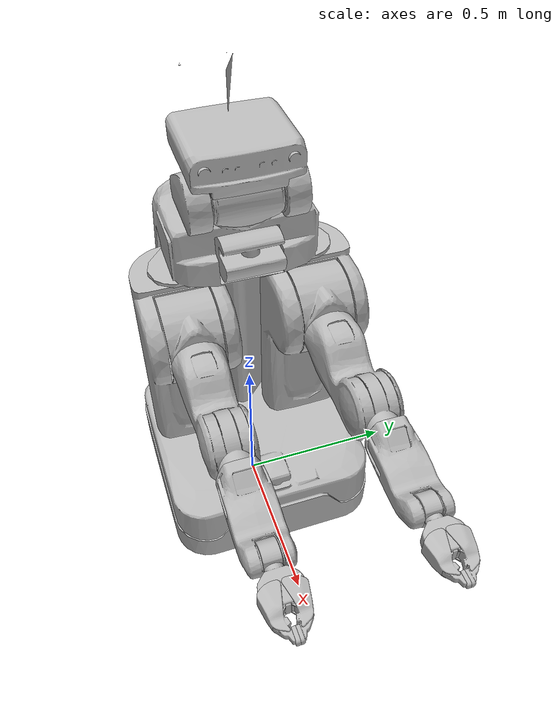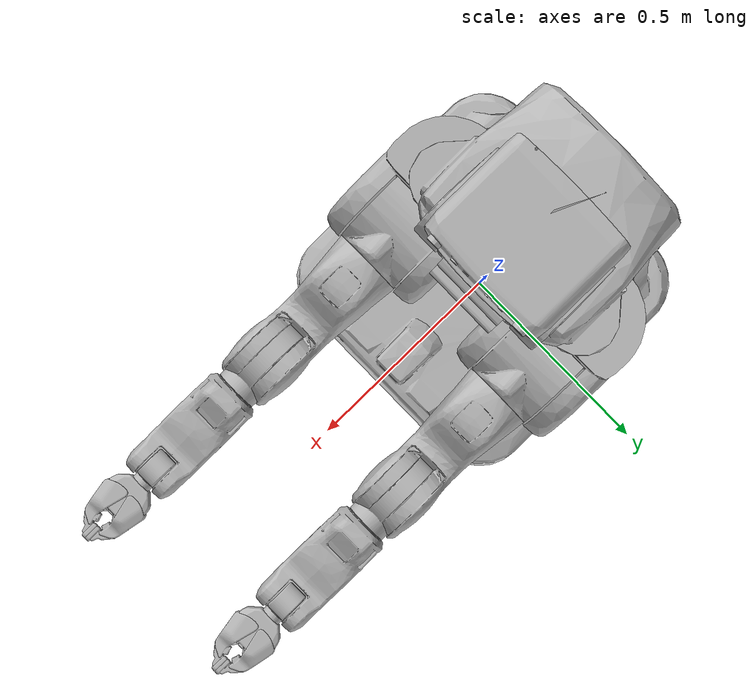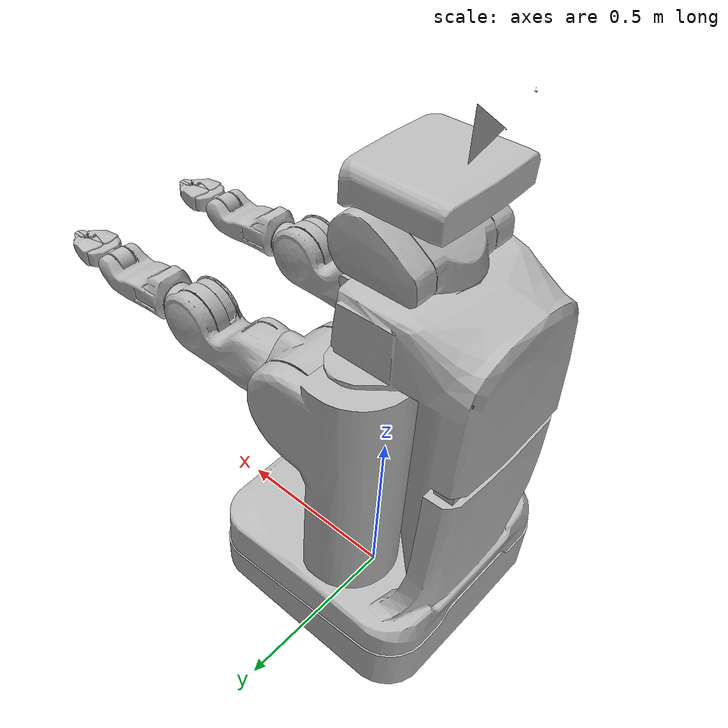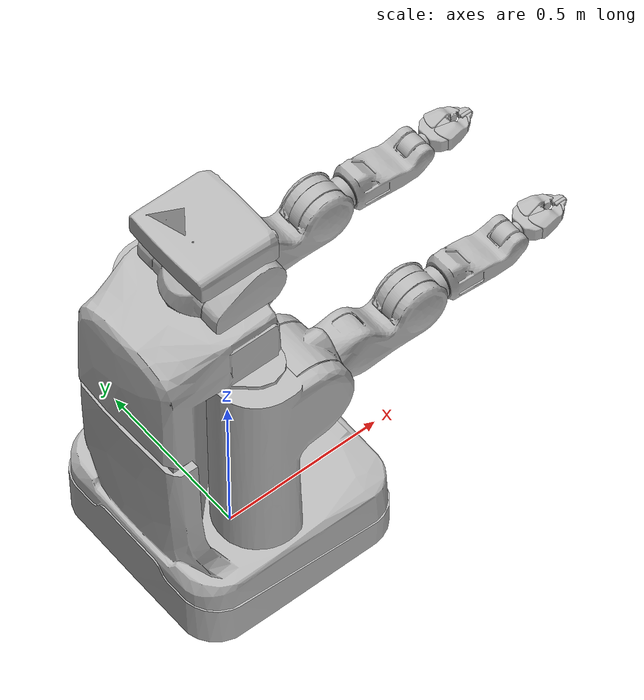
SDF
<?xml version="1.0" ?>
<sdf version='1.4'>
 <world name="default">
  <model name='pr2'>
    <static>0</static>
    <link name='base_footprint'>
      <self_collide>0</self_collide>
      <inertial>
        <mass>118.001000</mass>
        <pose>-0.062421 0.000000 0.201365 0.000000 -0.000000 0.000000</pose>
        <inertia>
          <ixx>8.431730</ixx>
          <ixy>-0.009720</ixy>
          <ixz>1.901570</ixz>
          <iyy>8.533050</iyy>
          <iyz>-0.007380</iyz>
          <izz>3.787470</izz>
        </inertia>
      </inertial>
      <collision name='base_footprint_geom'>
        <pose>0.000000 0.000000 0.071000 0.000000 -0.000000 0.000000</pose>
        <geometry>
          <box>
            <size>0.001000 0.001000 0.001000</size>
          </box>
        </geometry>
      </collision>
      <visual name='base_footprint_geom_visual'>
        <geometry>
          <box>
            <size>0.010000 0.010000 0.010000</size>
          </box>
        </geometry>
      </visual>
      <collision name='base_footprint_geom_base_bellow_link'>
        <pose>-0.290000 0.000000 0.851000 0.000000 -0.000000 0.000000</pose>
        <geometry>
          <box>
            <size>0.050000 0.370000 0.300000</size>
          </box>
        </geometry>
      </collision>
      <visual name='base_footprint_geom_base_bellow_link_visual'>
        <pose>-0.290000 0.000000 0.851000 0.000000 -0.000000 0.000000</pose>
        <geometry>
          <box>
            <size>0.050000 0.370000 0.300000</size>
          </box>
        </geometry>
      </visual>
      <collision name='base_footprint_geom_base_link'>
        <pose>0.000000 0.000000 0.051000 0.000000 -0.000000 0.000000</pose>
        <geometry>
          <mesh>
            <uri>model://pr2/meshes/base_v0/base_L.stl</uri>
          </mesh>
        </geometry>
      </collision>
      <visual name='base_footprint_geom_base_link_visual'>
        <pose>0.000000 0.000000 0.051000 0.000000 -0.000000 0.000000</pose>
        <geometry>
          <mesh>
            <uri>model://pr2/meshes/base_v0/base.dae</uri>
          </mesh>
        </geometry>
      </visual>
      <sensor name='base_contact_sensor' type='contact'>
        <update_rate>100.000000</update_rate>
        <contact>
          <collision>base_footprint_geom_base_link</collision>
          <topic>__default_topic__</topic>
        </contact>
        <plugin name='gazebo_contact' filename='libContactPlugin.so'/>
      </sensor>
      <sensor name='base_laser' type='ray'>
        <always_on>1</always_on>
        <visualize>1</visualize>
        <update_rate>20.000000</update_rate>
        <pose>0.275000 0.000000 0.303000 0.000000 -0.000000 0.000000</pose>
        <ray>
          <scan>
            <horizontal>
              <samples>640</samples>
              <resolution>1.000000</resolution>
              <min_angle>-2.268900</min_angle>
              <max_angle>2.268900</max_angle>
            </horizontal>
          </scan>
          <range>
            <min>0.080000</min>
            <max>10.000000</max>
            <resolution>0.010000</resolution>
          </range>
        </ray>
        <plugin name='laser' filename='libRayPlugin.so'/>
      </sensor>
      <velocity_decay/>
    </link>
    <link name='bl_caster_rotation_link'>
      <self_collide>0</self_collide>
      <pose>-0.224600 0.224600 0.079200 0.000000 -0.000000 0.000000</pose>
      <inertial>
        <mass>3.473080</mass>
        <pose>0.000000 0.000000 0.070000 0.000000 -0.000000 0.000000</pose>
        <inertia>
          <ixx>0.012412</ixx>
          <ixy>-0.000712</ixy>
          <ixz>0.000503</ixz>
          <iyy>0.015218</iyy>
          <iyz>-0.000004</iyz>
          <izz>0.011764</izz>
        </inertia>
      </inertial>
      <collision name='bl_caster_rotation_link_geom'>
        <geometry>
          <mesh>
            <uri>model://pr2/meshes/base_v0/caster_L.stl</uri>
          </mesh>
        </geometry>
      </collision>
      <visual name='bl_caster_rotation_link_geom_visual'>
        <geometry>
          <mesh>
            <uri>model://pr2/meshes/base_v0/caster.stl</uri>
          </mesh>
        </geometry>
      </visual>
      <velocity_decay/>
    </link>
    <link name='bl_caster_l_wheel_link'>
      <self_collide>0</self_collide>
      <pose>-0.224600 0.273600 0.079200 0.000000 -0.000000 0.000000</pose>
      <inertial>
        <mass>0.440360</mass>
        <inertia>
          <ixx>0.012412</ixx>
          <ixy>-0.000712</ixy>
          <ixz>0.000503</ixz>
          <iyy>0.015218</iyy>
          <iyz>-0.000004</iyz>
          <izz>0.011764</izz>
        </inertia>
      </inertial>
      <collision name='bl_caster_l_wheel_link_geom'>
        <pose>0.000000 0.000000 0.000000 1.570800 -0.000000 0.000000</pose>
        <geometry>
          <cylinder>
            <radius>0.074792</radius>
            <length>0.034000</length>
          </cylinder>
        </geometry>
      </collision>
      <visual name='bl_caster_l_wheel_link_geom_visual'>
        <geometry>
          <mesh>
            <uri>model://pr2/meshes/base_v0/wheel.dae</uri>
          </mesh>
        </geometry>
      </visual>
      <velocity_decay/>
    </link>
    <link name='bl_caster_r_wheel_link'>
      <self_collide>0</self_collide>
      <pose>-0.224600 0.175600 0.079200 0.000000 -0.000000 0.000000</pose>
      <inertial>
        <mass>0.440360</mass>
        <inertia>
          <ixx>0.012412</ixx>
          <ixy>0.000712</ixy>
          <ixz>0.000503</ixz>
          <iyy>0.015218</iyy>
          <iyz>0.000004</iyz>
          <izz>0.011764</izz>
        </inertia>
      </inertial>
      <collision name='bl_caster_r_wheel_link_geom'>
        <pose>0.000000 0.000000 0.000000 1.570800 -0.000000 0.000000</pose>
        <geometry>
          <cylinder>
            <radius>0.074792</radius>
            <length>0.034000</length>
          </cylinder>
        </geometry>
      </collision>
      <visual name='bl_caster_r_wheel_link_geom_visual'>
        <geometry>
          <mesh>
            <uri>model://pr2/meshes/base_v0/wheel.dae</uri>
          </mesh>
        </geometry>
      </visual>
      <velocity_decay/>
    </link>
    <link name='br_caster_rotation_link'>
      <self_collide>0</self_collide>
      <pose>-0.224600 -0.224600 0.079200 0.000000 -0.000000 0.000000</pose>
      <inertial>
        <mass>3.473080</mass>
        <pose>0.000000 0.000000 0.070000 0.000000 -0.000000 0.000000</pose>
        <inertia>
          <ixx>0.012412</ixx>
          <ixy>-0.000712</ixy>
          <ixz>0.000503</ixz>
          <iyy>0.015218</iyy>
          <iyz>-0.000004</iyz>
          <izz>0.011764</izz>
        </inertia>
      </inertial>
      <collision name='br_caster_rotation_link_geom'>
        <geometry>
          <mesh>
            <uri>./meshes/base_v0/caster_L.stl</uri>
          </mesh>
        </geometry>
      </collision>
      <visual name='br_caster_rotation_link_geom_visual'>
        <geometry>
          <mesh>
            <uri>./meshes/base_v0/caster.stl</uri>
          </mesh>
        </geometry>
      </visual>
      <velocity_decay/>
    </link>
    <link name='br_caster_l_wheel_link'>
      <self_collide>0</self_collide>
      <pose>-0.224600 -0.175600 0.079200 0.000000 -0.000000 0.000000</pose>
      <inertial>
        <mass>0.440360</mass>
        <inertia>
          <ixx>0.012412</ixx>
          <ixy>-0.000712</ixy>
          <ixz>0.000503</ixz>
          <iyy>0.015218</iyy>
          <iyz>-0.000004</iyz>
          <izz>0.011764</izz>
        </inertia>
      </inertial>
      <collision name='br_caster_l_wheel_link_geom'>
        <pose>0.000000 0.000000 0.000000 1.570800 -0.000000 0.000000</pose>
        <geometry>
          <cylinder>
            <radius>0.074792</radius>
            <length>0.034000</length>
          </cylinder>
        </geometry>
      </collision>
      <visual name='br_caster_l_wheel_link_geom_visual'>
        <geometry>
          <mesh>
            <uri>./meshes/base_v0/wheel.dae</uri>
          </mesh>
        </geometry>
      </visual>
      <velocity_decay/>
    </link>
    <link name='br_caster_r_wheel_link'>
      <self_collide>0</self_collide>
      <pose>-0.224600 -0.273600 0.079200 0.000000 -0.000000 0.000000</pose>
      <inertial>
        <mass>0.440360</mass>
        <inertia>
          <ixx>0.012412</ixx>
          <ixy>-0.000712</ixy>
          <ixz>0.000503</ixz>
          <iyy>0.015218</iyy>
          <iyz>-0.000004</iyz>
          <izz>0.011764</izz>
        </inertia>
      </inertial>
      <collision name='br_caster_r_wheel_link_geom'>
        <pose>0.000000 0.000000 0.000000 1.570800 -0.000000 0.000000</pose>
        <geometry>
          <cylinder>
            <radius>0.074792</radius>
            <length>0.034000</length>
          </cylinder>
        </geometry>
      </collision>
      <visual name='br_caster_r_wheel_link_geom_visual'>
        <geometry>
          <mesh>
            <uri>./meshes/base_v0/wheel.dae</uri>
          </mesh>
        </geometry>
      </visual>
      <velocity_decay/>
    </link>
    <link name='fl_caster_rotation_link'>
      <self_collide>0</self_collide>
      <pose>0.224600 0.224600 0.079200 0.000000 -0.000000 0.000000</pose>
      <inertial>
        <mass>3.473080</mass>
        <pose>0.000000 0.000000 0.070000 0.000000 -0.000000 0.000000</pose>
        <inertia>
          <ixx>0.012412</ixx>
          <ixy>-0.000712</ixy>
          <ixz>0.000503</ixz>
          <iyy>0.015218</iyy>
          <iyz>-0.000004</iyz>
          <izz>0.011764</izz>
        </inertia>
      </inertial>
      <collision name='fl_caster_rotation_link_geom'>
        <geometry>
          <mesh>
            <uri>./meshes/base_v0/caster_L.stl</uri>
          </mesh>
        </geometry>
      </collision>
      <visual name='fl_caster_rotation_link_geom_visual'>
        <geometry>
          <mesh>
            <uri>./meshes/base_v0/caster.stl</uri>
          </mesh>
        </geometry>
      </visual>
      <velocity_decay/>
    </link>
    <link name='fl_caster_l_wheel_link'>
      <self_collide>0</self_collide>
      <pose>0.224600 0.273600 0.079200 0.000000 -0.000000 0.000000</pose>
      <inertial>
        <mass>0.440360</mass>
        <inertia>
          <ixx>0.012412</ixx>
          <ixy>-0.000712</ixy>
          <ixz>0.000503</ixz>
          <iyy>0.015218</iyy>
          <iyz>-0.000004</iyz>
          <izz>0.011764</izz>
        </inertia>
      </inertial>
      <collision name='fl_caster_l_wheel_link_geom'>
        <pose>0.000000 0.000000 0.000000 1.570800 -0.000000 0.000000</pose>
        <geometry>
          <cylinder>
            <radius>0.074792</radius>
            <length>0.034000</length>
          </cylinder>
        </geometry>
      </collision>
      <visual name='fl_caster_l_wheel_link_geom_visual'>
        <geometry>
          <mesh>
            <uri>./meshes/base_v0/wheel.dae</uri>
          </mesh>
        </geometry>
      </visual>
      <velocity_decay/>
    </link>
    <link name='fl_caster_r_wheel_link'>
      <self_collide>0</self_collide>
      <pose>0.224600 0.175600 0.079200 0.000000 -0.000000 0.000000</pose>
      <inertial>
        <mass>0.440360</mass>
        <inertia>
          <ixx>0.012412</ixx>
          <ixy>-0.000712</ixy>
          <ixz>0.000503</ixz>
          <iyy>0.015218</iyy>
          <iyz>-0.000004</iyz>
          <izz>0.011764</izz>
        </inertia>
      </inertial>
      <collision name='fl_caster_r_wheel_link_geom'>
        <pose>0.000000 0.000000 0.000000 1.570800 -0.000000 0.000000</pose>
        <geometry>
          <cylinder>
            <radius>0.074792</radius>
            <length>0.034000</length>
          </cylinder>
        </geometry>
      </collision>
      <visual name='fl_caster_r_wheel_link_geom_visual'>
        <geometry>
          <mesh>
            <uri>./meshes/base_v0/wheel.dae</uri>
          </mesh>
        </geometry>
      </visual>
      <velocity_decay/>
    </link>
    <link name='fr_caster_rotation_link'>
      <self_collide>0</self_collide>
      <pose>0.224600 -0.224600 0.079200 0.000000 -0.000000 0.000000</pose>
      <inertial>
        <mass>3.473080</mass>
        <pose>0.000000 0.000000 0.070000 0.000000 -0.000000 0.000000</pose>
        <inertia>
          <ixx>0.012412</ixx>
          <ixy>-0.000712</ixy>
          <ixz>0.000503</ixz>
          <iyy>0.015218</iyy>
          <iyz>-0.000004</iyz>
          <izz>0.011764</izz>
        </inertia>
      </inertial>
      <collision name='fr_caster_rotation_link_geom'>
        <geometry>
          <mesh>
            <uri>./meshes/base_v0/caster_L.stl</uri>
          </mesh>
        </geometry>
      </collision>
      <visual name='fr_caster_rotation_link_geom_visual'>
        <geometry>
          <mesh>
            <uri>./meshes/base_v0/caster.stl</uri>
          </mesh>
        </geometry>
      </visual>
      <velocity_decay/>
    </link>
    <link name='fr_caster_l_wheel_link'>
      <self_collide>0</self_collide>
      <pose>0.224600 -0.175600 0.079200 0.000000 -0.000000 0.000000</pose>
      <inertial>
        <mass>0.440360</mass>
        <inertia>
          <ixx>0.012412</ixx>
          <ixy>-0.000712</ixy>
          <ixz>0.000503</ixz>
          <iyy>0.015218</iyy>
          <iyz>-0.000004</iyz>
          <izz>0.011764</izz>
        </inertia>
      </inertial>
      <collision name='fr_caster_l_wheel_link_geom'>
        <pose>0.000000 0.000000 0.000000 1.570800 -0.000000 0.000000</pose>
        <geometry>
          <cylinder>
            <radius>0.074792</radius>
            <length>0.034000</length>
          </cylinder>
        </geometry>
      </collision>
      <visual name='fr_caster_l_wheel_link_geom_visual'>
        <geometry>
          <mesh>
            <uri>./meshes/base_v0/wheel.dae</uri>
          </mesh>
        </geometry>
      </visual>
      <velocity_decay/>
    </link>
    <link name='fr_caster_r_wheel_link'>
      <self_collide>0</self_collide>
      <pose>0.224600 -0.273600 0.079200 0.000000 -0.000000 0.000000</pose>
      <inertial>
        <mass>0.440360</mass>
        <inertia>
          <ixx>0.012412</ixx>
          <ixy>-0.000712</ixy>
          <ixz>0.000503</ixz>
          <iyy>0.015218</iyy>
          <iyz>-0.000004</iyz>
          <izz>0.011764</izz>
        </inertia>
      </inertial>
      <collision name='fr_caster_r_wheel_link_geom'>
        <pose>0.000000 0.000000 0.000000 1.570800 -0.000000 0.000000</pose>
        <geometry>
          <cylinder>
            <radius>0.074792</radius>
            <length>0.034000</length>
          </cylinder>
        </geometry>
      </collision>
      <visual name='fr_caster_r_wheel_link_geom_visual'>
        <geometry>
          <mesh>
            <uri>./meshes/base_v0/wheel.dae</uri>
          </mesh>
        </geometry>
      </visual>
      <velocity_decay/>
    </link>
    <link name='torso_lift_link'>
      <self_collide>0</self_collide>
      <pose>-0.050000 0.000000 0.790675 0.000000 -0.000000 0.000000</pose>
      <inertial>
        <mass>36.449000</mass>
        <pose>-0.099499 -0.000004 -0.086764 0.000000 -0.000000 0.000000</pose>
        <inertia>
          <ixx>2.792330</ixx>
          <ixy>0.004280</ixy>
          <ixz>-0.160631</ixz>
          <iyy>2.521060</iyy>
          <iyz>0.029689</iyz>
          <izz>0.536551</izz>
        </inertia>
      </inertial>
      <collision name='torso_lift_link_geom'>
        <geometry>
          <mesh>
            <uri>./meshes/torso_v0/torso_lift_L.stl</uri>
          </mesh>
        </geometry>
      </collision>
      <visual name='torso_lift_link_geom_visual'>
        <geometry>
          <mesh>
            <uri>./meshes/torso_v0/torso_lift.dae</uri>
          </mesh>
        </geometry>
      </visual>
      <sensor name='torso_lift_contact_sensor' type='contact'>
        <update_rate>100.000000</update_rate>
        <contact>
          <collision>torso_lift_link_geom</collision>
          <topic>__default_topic__</topic>
        </contact>
      </sensor>
      <velocity_decay/>
    </link>
    <link name='head_pan_link'>
      <self_collide>0</self_collide>
      <pose>-0.067070 0.000000 1.172130 0.000000 -0.000000 0.000000</pose>
      <inertial>
        <mass>6.339000</mass>
        <pose>0.010907 0.031693 0.090507 0.000000 -0.000000 0.000000</pose>
        <inertia>
          <ixx>0.032498</ixx>
          <ixy>0.000636</ixy>
          <ixz>0.002585</ixz>
          <iyy>0.046546</iyy>
          <iyz>-0.002453</iyz>
          <izz>0.057653</izz>
        </inertia>
      </inertial>
      <collision name='head_pan_link_geom'>
        <geometry>
          <mesh>
            <uri>./meshes/head_v0/head_pan_L.stl</uri>
          </mesh>
        </geometry>
      </collision>
      <visual name='head_pan_link_geom_visual'>
        <geometry>
          <mesh>
            <uri>./meshes/head_v0/head_pan.dae</uri>
          </mesh>
        </geometry>
      </visual>
      <velocity_decay/>
    </link>
    <link name='head_tilt_link'>
      <projector name='projector_wg6802418_projector_wg6802418'>
        <texture>stereo_projection_pattern_high_res_red.png</texture>
        <fov>0.959931</fov>
        <near_clip>0.100000</near_clip>
        <far_clip>10.000000</far_clip>
        <pose>0.023200 0.110000 0.119100 0 -1.570793 0</pose>
      </projector>

      <self_collide>0</self_collide>
      <pose>0.000930 0.000000 1.172130 0.000000 -0.000000 0.000000</pose>
      <inertial>
        <mass>5.319000</mass>
        <pose>-0.005151 -0.014635 0.072819 0.000000 -0.000000 0.000000</pose>
        <inertia>
          <ixx>0.126134</ixx>
          <ixy>0.000237</ixy>
          <ixz>0.011881</ixz>
          <iyy>0.165102</iyy>
          <iyz>0.001606</iyz>
          <izz>0.166947</izz>
        </inertia>
      </inertial>
      <collision name='head_tilt_link_geom'>
        <geometry>
          <mesh>
            <uri>./meshes/head_v0/head_tilt_L.stl</uri>
          </mesh>
        </geometry>
      </collision>
      <visual name='head_tilt_link_geom_visual'>
        <geometry>
          <mesh>
            <uri>./meshes/head_v0/head_tilt.dae</uri>
          </mesh>
        </geometry>
      </visual>
      <collision name='head_tilt_link_geom_head_mount_kinect_ir_link'>
        <pose>-0.147067 0.012500 0.291953 0.000000 -0.000000 0.000000</pose>
        <geometry>
          <sphere>
            <radius>0.000500</radius>
          </sphere>
        </geometry>
      </collision>
      <visual name='head_tilt_link_geom_head_mount_kinect_ir_link_visual'>
        <pose>-0.147067 0.012500 0.291953 0.000000 -0.000000 0.000000</pose>
        <geometry>
          <sphere>
            <radius>0.000250</radius>
          </sphere>
        </geometry>
        <material>
          <script>Gazebo/Red</script>
        </material>
      </visual>
      <collision name='head_tilt_link_geom_head_mount_kinect_rgb_link'>
        <pose>-0.147067 0.017500 0.291953 0.000000 -0.000000 0.000000</pose>
        <geometry>
          <sphere>
            <radius>0.000500</radius>
          </sphere>
        </geometry>
      </collision>
      <visual name='head_tilt_link_geom_head_mount_kinect_rgb_link_visual'>
        <pose>-0.147067 0.017500 0.291953 0.000000 -0.000000 0.000000</pose>
        <geometry>
          <sphere>
            <radius>0.000250</radius>
          </sphere>
        </geometry>
        <material>
          <script>Gazebo/Red</script>
        </material>
      </visual>
      <collision name='head_tilt_link_geom_head_mount_link'>
        <pose>-0.114800 0.000000 0.155500 0.000000 -0.000000 0.000000</pose>
        <geometry>
          <sphere>
            <radius>0.000500</radius>
          </sphere>
        </geometry>
      </collision>
      <visual name='head_tilt_link_geom_head_mount_link_visual'>
        <pose>-0.114800 0.000000 0.155500 0.000000 -0.000000 0.000000</pose>
        <geometry>
          <mesh>
            <uri>./meshes/sensors/kinect_prosilica_v0/115x100_swept_back--coarse.STL</uri>
            <scale>0.001000 0.001000 0.001000</scale>
          </mesh>
        </geometry>
      </visual>
      <collision name='head_tilt_link_geom_head_mount_prosilica_link'>
        <pose>-0.161257 0.012500 0.244421 0.000000 -0.000000 0.000000</pose>
        <geometry>
          <sphere>
            <radius>0.000500</radius>
          </sphere>
        </geometry>
      </collision>
      <visual name='head_tilt_link_geom_head_mount_prosilica_link_visual'>
        <pose>-0.161257 0.012500 0.244421 0.000000 -0.000000 0.000000</pose>
        <geometry>
          <sphere>
            <radius>0.000250</radius>
          </sphere>
        </geometry>
        <material>
          <script>Gazebo/Red</script>
        </material>
      </visual>
      <collision name='head_tilt_link_geom_head_plate_frame'>
        <pose>0.023200 0.000000 0.064500 0.000000 -0.000000 0.000000</pose>
        <geometry>
          <box>
            <size>0.010000 0.010000 0.010000</size>
          </box>
        </geometry>
      </collision>
      <visual name='head_tilt_link_geom_head_plate_frame_visual'>
        <pose>0.023200 0.000000 0.064500 0.000000 -0.000000 0.000000</pose>
        <geometry>
          <box>
            <size>0.010000 0.010000 0.010000</size>
          </box>
        </geometry>
        <material>
          <script>Gazebo/Grey</script>
        </material>
      </visual>
      <sensor name='head_mount_sensor' type='camera'>
        <always_on>0</always_on>
        <visualize>0</visualize>
        <update_rate>1.000000</update_rate>
        <pose>-0.147067 0.012500 0.291953 0.000000 -0.000000 0.000000</pose>
        <camera>
          <horizontal_fov>0.994838</horizontal_fov>
          <image>
            <width>640</width>
            <height>480</height>
            <format>L8</format>
          </image>
          <clip>
            <near>0.010000</near>
            <far>5.000000</far>
          </clip>
        </camera>
      </sensor>
      <sensor name='head_mount_prosilica_link_sensor' type='camera'>
        <update_rate>1.000000</update_rate>
        <pose>-0.161257 0.012500 0.244421 0.000000 -0.000000 0.000000</pose>
        <camera>
          <horizontal_fov>1.120501</horizontal_fov>
          <image>
            <width>320</width>
            <height>240</height>
            <format>R8G8B8</format>
          </image>
          <clip>
            <near>0.100000</near>
            <far>100.000000</far>
          </clip>
        </camera>
      </sensor>
      <sensor name='head_mount_prosilica_link_sim_pcd_sensor' type='camera'>
        <update_rate>1.000000</update_rate>
        <pose>-0.161257 0.012500 0.244421 0.000000 -0.000000 0.000000</pose>
        <camera>
          <horizontal_fov>1.120501</horizontal_fov>
          <image>
            <width>320</width>
            <height>240</height>
            <format>R8G8B8</format>
          </image>
          <clip>
            <near>0.100000</near>
            <far>100.000000</far>
          </clip>
        </camera>
      </sensor>
      <sensor name='narrow_stereo_gazebo_l_stereo_camera_sensor' type='camera'>
        <always_on>1</always_on>
        <visualize>1</visualize>
        <update_rate>25.000000</update_rate>
        <pose>0.068200 0.060000 0.114600 0.000000 -0.000000 0.000000</pose>
        <camera>
          <horizontal_fov>0.785398</horizontal_fov>
          <image>
            <width>640</width>
            <height>480</height>
            <format>L8</format>
          </image>
          <clip>
            <near>0.100000</near>
            <far>100.000000</far>
          </clip>
        </camera>
      </sensor>
      <sensor name='narrow_stereo_gazebo_r_stereo_camera_sensor' type='camera'>
        <always_on>1</always_on>
        <update_rate>25.000000</update_rate>
        <pose>0.068200 -0.030000 0.114600 0.000000 -0.000000 0.000000</pose>
        <camera>
          <horizontal_fov>0.785398</horizontal_fov>
          <image>
            <width>640</width>
            <height>480</height>
            <format>L8</format>
          </image>
          <clip>
            <near>0.100000</near>
            <far>100.000000</far>
          </clip>
        </camera>
      </sensor>
      <sensor name='wide_stereo_gazebo_l_stereo_camera_sensor' type='camera'>
        <update_rate>25.000000</update_rate>
        <pose>0.068200 0.030000 0.114600 0.000000 -0.000000 0.000000</pose>
        <camera>
          <horizontal_fov>1.570796</horizontal_fov>
          <image>
            <width>640</width>
            <height>480</height>
            <format>BAYER_BGGR8</format>
          </image>
          <clip>
            <near>0.100000</near>
            <far>100.000000</far>
          </clip>
        </camera>
      </sensor>
      <sensor name='wide_stereo_gazebo_r_stereo_camera_sensor' type='camera'>
        <update_rate>25.000000</update_rate>
        <pose>0.068200 -0.060000 0.114600 0.000000 -0.000000 0.000000</pose>
        <camera>
          <horizontal_fov>1.570796</horizontal_fov>
          <image>
            <width>640</width>
            <height>480</height>
            <format>BAYER_BGGR8</format>
          </image>
          <clip>
            <near>0.100000</near>
            <far>100.000000</far>
          </clip>
        </camera>
      </sensor>
      <sensor name='high_def_sensor' type='camera'>
        <update_rate>20.000000</update_rate>
        <pose>0.069657 -0.110000 0.119100 0.000000 -0.000000 0.000000</pose>
        <camera>
          <horizontal_fov>0.785398</horizontal_fov>
          <image>
            <width>2448</width>
            <height>2050</height>
            <format>R8G8B8</format>
          </image>
          <clip>
            <near>0.100000</near>
            <far>100.000000</far>
          </clip>
        </camera>
      </sensor>
      <velocity_decay/>
    </link>
    <link name='l_shoulder_pan_link'>
      <self_collide>0</self_collide>
      <gravity>0</gravity>
      <pose>-0.050000 0.188000 0.790675 0.000000 -0.000000 0.000000</pose>
      <inertial>
        <mass>25.799300</mass>
        <pose>-0.001201 0.024513 -0.098231 0.000000 -0.000000 0.000000</pose>
        <inertia>
          <ixx>0.866179</ixx>
          <ixy>-0.060865</ixy>
          <ixz>-0.121181</ixz>
          <iyy>0.874217</iyy>
          <iyz>-0.058866</iyz>
          <izz>0.273538</izz>
        </inertia>
      </inertial>
      <collision name='l_shoulder_pan_link_geom'>
        <geometry>
          <mesh>
            <uri>./meshes/shoulder_v0/shoulder_pan.stl</uri>
          </mesh>
        </geometry>
      </collision>
      <visual name='l_shoulder_pan_link_geom_visual'>
        <geometry>
          <mesh>
            <uri>./meshes/shoulder_v0/shoulder_pan.dae</uri>
          </mesh>
        </geometry>
      </visual>
      <velocity_decay/>
    </link>
    <link name='l_shoulder_lift_link'>
      <self_collide>0</self_collide>
      <gravity>0</gravity>
      <pose>0.050000 0.188000 0.790675 0.000000 -0.000000 0.000000</pose>
      <inertial>
        <mass>2.749880</mass>
        <pose>0.021950 -0.026640 -0.031270 0.000000 -0.000000 0.000000</pose>
        <inertia>
          <ixx>0.021056</ixx>
          <ixy>0.004967</ixy>
          <ixz>-0.001948</ixz>
          <iyy>0.021272</iyy>
          <iyz>0.001104</iyz>
          <izz>0.019758</izz>
        </inertia>
      </inertial>
      <collision name='l_shoulder_lift_link_geom'>
        <geometry>
          <mesh>
            <uri>./meshes/shoulder_v0/shoulder_lift.stl</uri>
          </mesh>
        </geometry>
      </collision>
      <visual name='l_shoulder_lift_link_geom_visual'>
        <geometry>
          <mesh>
            <uri>./meshes/shoulder_v0/shoulder_lift.dae</uri>
          </mesh>
        </geometry>
      </visual>
      <velocity_decay/>
    </link>
    <link name='l_upper_arm_roll_link'>
      <self_collide>0</self_collide>
      <gravity>0</gravity>
      <pose>0.050000 0.188000 0.790675 0.000000 -0.000000 0.000000</pose>
      <inertial>
        <mass>6.117690</mass>
        <pose>0.210551 0.016309 -0.000561 0.000000 -0.000000 0.000000</pose>
        <inertia>
          <ixx>0.025306</ixx>
          <ixy>-0.003393</ixy>
          <ixz>0.000608</ixz>
          <iyy>0.084737</iyy>
          <iyz>-0.000200</iyz>
          <izz>0.086016</izz>
        </inertia>
      </inertial>
      <collision name='l_upper_arm_roll_link_geom'>
        <geometry>
          <mesh>
            <uri>./meshes/shoulder_v0/upper_arm_roll_L.stl</uri>
          </mesh>
        </geometry>
      </collision>
      <visual name='l_upper_arm_roll_link_geom_visual'>
        <geometry>
          <mesh>
            <uri>./meshes/shoulder_v0/upper_arm_roll.stl</uri>
          </mesh>
        </geometry>
      </visual>
      <collision name='l_upper_arm_roll_link_geom_l_upper_arm_link'>
        <geometry>
          <mesh>
            <uri>./meshes/upper_arm_v0/upper_arm.stl</uri>
          </mesh>
        </geometry>
      </collision>
      <visual name='l_upper_arm_roll_link_geom_l_upper_arm_link_visual'>
        <geometry>
          <mesh>
            <uri>./meshes/upper_arm_v0/upper_arm.dae</uri>
          </mesh>
        </geometry>
      </visual>
      <velocity_decay/>
    </link>
    <link name='l_elbow_flex_link'>
      <self_collide>0</self_collide>
      <gravity>0</gravity>
      <pose>0.450000 0.188000 0.790675 0.000000 -0.000000 0.000000</pose>
      <inertial>
        <mass>1.903270</mass>
        <pose>0.010140 0.000320 -0.012110 0.000000 -0.000000 0.000000</pose>
        <inertia>
          <ixx>0.003465</ixx>
          <ixy>0.000041</ixy>
          <ixz>0.000432</ixz>
          <iyy>0.004416</iyy>
          <iyz>-0.000040</iyz>
          <izz>0.003592</izz>
        </inertia>
      </inertial>
      <collision name='l_elbow_flex_link_geom'>
        <geometry>
          <mesh>
            <uri>./meshes/upper_arm_v0/elbow_flex.stl</uri>
          </mesh>
        </geometry>
      </collision>
      <visual name='l_elbow_flex_link_geom_visual'>
        <geometry>
          <mesh>
            <uri>./meshes/upper_arm_v0/elbow_flex.dae</uri>
          </mesh>
        </geometry>
      </visual>
      <velocity_decay/>
    </link>
    <link name='l_forearm_roll_link'>
      <self_collide>0</self_collide>
      <gravity>0</gravity>
      <pose>0.450000 0.188000 0.790675 0.000000 -0.000000 0.000000</pose>
      <inertial>
        <mass>2.689680</mass>
        <pose>0.180727 -0.000163 -0.008583 0.000000 -0.000000 0.000000</pose>
        <inertia>
          <ixx>0.014668</ixx>
          <ixy>0.000052</ixy>
          <ixz>0.000656</ixz>
          <iyy>0.026279</iyy>
          <iyz>-0.000013</iyz>
          <izz>0.027775</izz>
        </inertia>
      </inertial>
      <collision name='l_forearm_roll_link_geom'>
        <geometry>
          <mesh>
            <uri>./meshes/upper_arm_v0/forearm_roll_L.stl</uri>
          </mesh>
        </geometry>
      </collision>
      <visual name='l_forearm_roll_link_geom_visual'>
        <geometry>
          <mesh>
            <uri>./meshes/upper_arm_v0/forearm_roll.stl</uri>
          </mesh>
        </geometry>
      </visual>
      <collision name='l_forearm_roll_link_geom_l_forearm_link'>
        <geometry>
          <mesh>
            <uri>./meshes/forearm_v0/forearm.stl</uri>
          </mesh>
        </geometry>
      </collision>
      <visual name='l_forearm_roll_link_geom_l_forearm_link_visual'>
        <geometry>
          <mesh>
            <uri>./meshes/forearm_v0/forearm.dae</uri>
          </mesh>
        </geometry>
      </visual>
      <sensor name='l_forearm_cam_sensor' type='camera'>
        <update_rate>25.000000</update_rate>
        <pose>0.135000 0.000000 0.044000 -1.570800 -0.562869 0.000000</pose>
        <camera>
          <horizontal_fov>1.570796</horizontal_fov>
          <image>
            <width>640</width>
            <height>480</height>
            <format>R8G8B8</format>
          </image>
          <clip>
            <near>0.100000</near>
            <far>100.000000</far>
          </clip>
        </camera>
      </sensor>
      <velocity_decay/>
    </link>
    <link name='l_wrist_flex_link'>
      <self_collide>0</self_collide>
      <gravity>0</gravity>
      <pose>0.771000 0.188000 0.790675 0.000000 -0.000000 0.000000</pose>
      <inertial>
        <mass>0.614020</mass>
        <pose>-0.001570 0.000000 -0.000750 0.000000 -0.000000 0.000000</pose>
        <inertia>
          <ixx>0.000652</ixx>
          <ixy>0.000000</ixy>
          <ixz>0.000003</ixz>
          <iyy>0.000198</iyy>
          <iyz>0.000000</iyz>
          <izz>0.000645</izz>
        </inertia>
      </inertial>
      <collision name='l_wrist_flex_link_geom'>
        <geometry>
          <mesh>
            <uri>./meshes/forearm_v0/wrist_flex.stl</uri>
          </mesh>
        </geometry>
      </collision>
      <visual name='l_wrist_flex_link_geom_visual'>
        <geometry>
          <mesh>
            <uri>./meshes/forearm_v0/wrist_flex.dae</uri>
          </mesh>
        </geometry>
      </visual>
      <velocity_decay/>
    </link>
    <link name='l_wrist_roll_link'>
      <self_collide>0</self_collide>
      <gravity>0</gravity>
      <pose>0.771000 0.188000 0.790675 0.000000 -0.000000 0.000000</pose>
      <inertial>
        <mass>0.681070</mass>
        <pose>0.056408 0.000451 -0.001014 0.000000 -0.000000 0.000000</pose>
        <inertia>
          <ixx>0.011352</ixx>
          <ixy>-0.000016</ixy>
          <ixz>-0.000001</ixz>
          <iyy>0.011677</iyy>
          <iyz>-0.000001</iyz>
          <izz>0.011866</izz>
        </inertia>
      </inertial>
      <collision name='l_wrist_roll_link_geom'>
        <geometry>
          <mesh>
            <uri>./meshes/forearm_v0/wrist_roll_L.stl</uri>
          </mesh>
        </geometry>
      </collision>
      <visual name='l_wrist_roll_link_geom_visual'>
        <geometry>
          <mesh>
            <uri>./meshes/forearm_v0/wrist_roll.stl</uri>
          </mesh>
        </geometry>
      </visual>
      <collision name='l_wrist_roll_link_geom_l_gripper_motor_accelerometer_link'>
        <geometry>
          <box>
            <size>0.001000 0.001000 0.001000</size>
          </box>
        </geometry>
      </collision>
      <visual name='l_wrist_roll_link_geom_l_gripper_motor_accelerometer_link_visual'>
        <geometry>
          <box>
            <size>0.001000 0.001000 0.001000</size>
          </box>
        </geometry>
      </visual>
      <collision name='l_wrist_roll_link_geom_l_gripper_palm_link'>
        <geometry>
          <mesh>
            <uri>./meshes/gripper_v0/gripper_palm.stl</uri>
          </mesh>
        </geometry>
      </collision>
      <visual name='l_wrist_roll_link_geom_l_gripper_palm_link_visual'>
        <geometry>
          <mesh>
            <uri>./meshes/gripper_v0/gripper_palm.dae</uri>
          </mesh>
        </geometry>
      </visual>
      <velocity_decay/>
    </link>
    <link name='l_gripper_l_finger_link'>
      <self_collide>0</self_collide>
      <gravity>0</gravity>
      <pose>0.847910 0.198000 0.790675 0.000000 -0.000000 0.000000</pose>
      <inertial>
        <mass>0.171260</mass>
        <pose>0.035980 0.017300 -0.001640 0.000000 -0.000000 0.000000</pose>
        <inertia>
          <ixx>0.000078</ixx>
          <ixy>0.000001</ixy>
          <ixz>-0.000010</ixz>
          <iyy>0.000197</iyy>
          <iyz>-0.000003</iyz>
          <izz>0.000181</izz>
        </inertia>
      </inertial>
      <collision name='l_gripper_l_finger_link_geom'>
        <geometry>
          <mesh>
            <uri>./meshes/gripper_v0/l_finger.stl</uri>
          </mesh>
        </geometry>
        <surface>
          <friction>
            <ode>
              <mu>500.000000</mu>
              <mu2>500.000000</mu2>
              <slip1>0.000000</slip1>
              <slip2>0.000000</slip2>
            </ode>
          </friction>
          <contact>
            <ode>
              <kp>1000000.000000</kp>
              <kd>1.000000</kd>
              <max_vel>100.000000</max_vel>
              <min_depth>0.000000</min_depth>
            </ode>
          </contact>
        </surface>
      </collision>
      <visual name='l_gripper_l_finger_link_geom_visual'>
        <geometry>
          <mesh>
            <uri>./meshes/gripper_v0/l_finger.dae</uri>
          </mesh>
        </geometry>
      </visual>
      <velocity_decay/>
    </link>
    <link name='l_gripper_l_finger_tip_link'>
      <self_collide>0</self_collide>
      <gravity>0</gravity>
      <pose>0.939280 0.202950 0.790675 0.000000 -0.000000 0.000000</pose>
      <inertial>
        <mass>0.044190</mass>
        <pose>0.004230 0.002840 0.000000 0.000000 -0.000000 0.000000</pose>
        <inertia>
          <ixx>0.000008</ixx>
          <ixy>0.000006</ixy>
          <ixz>0.000000</ixz>
          <iyy>0.000010</iyy>
          <iyz>0.000000</iyz>
          <izz>0.000015</izz>
        </inertia>
      </inertial>
      <collision name='l_gripper_l_finger_tip_link_geom'>
        <geometry>
          <mesh>
            <uri>./meshes/gripper_v0/l_finger_tip.stl</uri>
          </mesh>
        </geometry>
        <surface>
          <friction>
            <ode>
              <mu>500.000000</mu>
              <mu2>500.000000</mu2>
              <slip1>0.000000</slip1>
              <slip2>0.000000</slip2>
            </ode>
          </friction>
          <contact>
            <ode>
              <kp>10000000.000000</kp>
              <kd>1.000000</kd>
              <max_vel>100.000000</max_vel>
              <min_depth>0.000000</min_depth>
            </ode>
          </contact>
        </surface>
      </collision>
      <visual name='l_gripper_l_finger_tip_link_geom_visual'>
        <geometry>
          <mesh>
            <uri>./meshes/gripper_v0/l_finger_tip.dae</uri>
          </mesh>
        </geometry>
      </visual>
      <sensor name='l_gripper_l_finger_tip_contact_sensor' type='contact'>
        <update_rate>100.000000</update_rate>
        <contact>
          <collision>l_gripper_l_finger_tip_link_geom</collision>
          <topic>__default_topic__</topic>
        </contact>
      </sensor>
      <velocity_decay/>
    </link>
    <link name='l_gripper_motor_slider_link'>
      <self_collide>0</self_collide>
      <gravity>0</gravity>
      <pose>0.939280 0.188000 0.790675 0.000000 -0.000000 0.000000</pose>
      <inertial>
        <mass>0.010000</mass>
        <inertia>
          <ixx>0.001000</ixx>
          <ixy>0.000000</ixy>
          <ixz>0.000000</ixz>
          <iyy>0.001000</iyy>
          <iyz>0.000000</iyz>
          <izz>0.001000</izz>
        </inertia>
      </inertial>
      <velocity_decay/>
    </link>
    <link name='l_gripper_motor_screw_link'>
      <self_collide>0</self_collide>
      <gravity>0</gravity>
      <pose>0.939280 0.188000 0.790675 0.000000 -0.000000 0.000000</pose>
      <inertial>
        <mass>0.010000</mass>
        <inertia>
          <ixx>0.000100</ixx>
          <ixy>0.000000</ixy>
          <ixz>0.000000</ixz>
          <iyy>0.000100</iyy>
          <iyz>0.000000</iyz>
          <izz>0.000100</izz>
        </inertia>
      </inertial>
      <velocity_decay/>
    </link>
    <link name='l_gripper_r_finger_link'>
      <self_collide>0</self_collide>
      <gravity>0</gravity>
      <pose>0.847910 0.178000 0.790675 0.000000 -0.000000 0.000000</pose>
      <inertial>
        <mass>0.173890</mass>
        <pose>0.035760 -0.017360 -0.000950 0.000000 -0.000000 0.000000</pose>
        <inertia>
          <ixx>0.000077</ixx>
          <ixy>-0.000002</ixy>
          <ixz>-0.000008</ixz>
          <iyy>0.000198</iyy>
          <iyz>0.000002</iyz>
          <izz>0.000181</izz>
        </inertia>
      </inertial>
      <collision name='l_gripper_r_finger_link_geom'>
        <pose>0.000000 0.000000 0.000000 -3.141590 0.000000 0.000000</pose>
        <geometry>
          <mesh>
            <uri>./meshes/gripper_v0/l_finger.stl</uri>
          </mesh>
        </geometry>
        <surface>
          <friction>
            <ode>
              <mu>500.000000</mu>
              <mu2>500.000000</mu2>
              <slip1>0.000000</slip1>
              <slip2>0.000000</slip2>
            </ode>
          </friction>
          <contact>
            <ode>
              <kp>1000000.000000</kp>
              <kd>1.000000</kd>
              <max_vel>100.000000</max_vel>
              <min_depth>0.000000</min_depth>
            </ode>
          </contact>
        </surface>
      </collision>
      <visual name='l_gripper_r_finger_link_geom_visual'>
        <pose>0.000000 0.000000 0.000000 -3.141590 0.000000 0.000000</pose>
        <geometry>
          <mesh>
            <uri>./meshes/gripper_v0/l_finger.dae</uri>
          </mesh>
        </geometry>
      </visual>
      <velocity_decay/>
    </link>
    <link name='l_gripper_r_finger_tip_link'>
      <self_collide>0</self_collide>
      <gravity>0</gravity>
      <pose>0.939280 0.173050 0.790675 0.000000 -0.000000 0.000000</pose>
      <inertial>
        <mass>0.044190</mass>
        <pose>0.004230 -0.002840 0.000000 0.000000 -0.000000 0.000000</pose>
        <inertia>
          <ixx>0.000008</ixx>
          <ixy>-0.000006</ixy>
          <ixz>0.000000</ixz>
          <iyy>0.000010</iyy>
          <iyz>0.000000</iyz>
          <izz>0.000015</izz>
        </inertia>
      </inertial>
      <collision name='l_gripper_r_finger_tip_link_geom'>
        <pose>0.000000 0.000000 0.000000 -3.141590 0.000000 0.000000</pose>
        <geometry>
          <mesh>
            <uri>./meshes/gripper_v0/l_finger_tip.stl</uri>
          </mesh>
        </geometry>
        <surface>
          <friction>
            <ode>
              <mu>500.000000</mu>
              <mu2>500.000000</mu2>
              <slip1>0.000000</slip1>
              <slip2>0.000000</slip2>
            </ode>
          </friction>
          <contact>
            <ode>
              <kp>10000000.000000</kp>
              <kd>1.000000</kd>
              <max_vel>100.000000</max_vel>
              <min_depth>0.000000</min_depth>
            </ode>
          </contact>
        </surface>
      </collision>
      <visual name='l_gripper_r_finger_tip_link_geom_visual'>
        <pose>0.000000 0.000000 0.000000 -3.141590 0.000000 0.000000</pose>
        <geometry>
          <mesh>
            <uri>./meshes/gripper_v0/l_finger_tip.dae</uri>
          </mesh>
        </geometry>
      </visual>
      <sensor name='l_gripper_r_finger_tip_contact_sensor' type='contact'>
        <update_rate>100.000000</update_rate>
        <contact>
          <collision>l_gripper_r_finger_tip_link_geom</collision>
          <topic>__default_topic__</topic>
        </contact>
      </sensor>
      <velocity_decay/>
    </link>
    <link name='laser_tilt_mount_link'>
      <self_collide>0</self_collide>
      <pose>0.048930 0.000000 1.017680 0.000000 -0.000000 0.000000</pose>
      <inertial>
        <mass>0.592000</mass>
        <pose>-0.001134 0.001667 -0.007067 0.000000 -0.000000 0.000000</pose>
        <inertia>
          <ixx>0.001296</ixx>
          <ixy>0.000023</ixy>
          <ixz>0.000037</ixz>
          <iyy>0.001086</iyy>
          <iyz>0.000035</iyz>
          <izz>0.000895</izz>
        </inertia>
      </inertial>
      <collision name='laser_tilt_mount_link_geom'>
        <geometry>
          <mesh>
            <uri>./meshes/tilting_laser_v0/tilting_hokuyo_L.stl</uri>
          </mesh>
        </geometry>
        <surface>
          <friction>
            <ode>
              <mu>0.000000</mu>
              <mu2>0.000000</mu2>
              <slip1>0.000000</slip1>
              <slip2>0.000000</slip2>
            </ode>
          </friction>
          <contact>
            <ode>
              <kp>1000000000000.000000</kp>
              <kd>10000.000000</kd>
              <max_vel>100.000000</max_vel>
              <min_depth>0.000000</min_depth>
            </ode>
          </contact>
        </surface>
      </collision>
      <visual name='laser_tilt_mount_link_geom_visual'>
        <geometry>
          <mesh>
            <uri>./meshes/tilting_laser_v0/tilting_hokuyo.dae</uri>
          </mesh>
        </geometry>
      </visual>
      <sensor name='laser_tilt' type='ray'>
        <update_rate>40.000000</update_rate>
        <pose>0.000000 0.000000 0.030000 0.000000 -0.000000 0.000000</pose>
        <ray>
          <scan>
            <horizontal>
              <samples>640</samples>
              <resolution>1.000000</resolution>
              <min_angle>-1.396263</min_angle>
              <max_angle>1.396263</max_angle>
            </horizontal>
          </scan>
          <range>
            <min>0.080000</min>
            <max>10.000000</max>
            <resolution>0.010000</resolution>
          </range>
        </ray>
      </sensor>
      <velocity_decay/>
    </link>
    <link name='r_shoulder_pan_link'>
      <self_collide>0</self_collide>
      <gravity>0</gravity>
      <pose>-0.050000 -0.188000 0.790675 0.000000 -0.000000 0.000000</pose>
      <inertial>
        <mass>25.799300</mass>
        <pose>-0.001201 0.024513 -0.098231 0.000000 -0.000000 0.000000</pose>
        <inertia>
          <ixx>0.866179</ixx>
          <ixy>-0.060865</ixy>
          <ixz>-0.121181</ixz>
          <iyy>0.874217</iyy>
          <iyz>-0.058866</iyz>
          <izz>0.273538</izz>
        </inertia>
      </inertial>
      <collision name='r_shoulder_pan_link_geom'>
        <geometry>
          <mesh>
            <uri>./meshes/shoulder_v0/shoulder_pan.stl</uri>
          </mesh>
        </geometry>
        <surface>
          <friction>
            <ode>
              <mu>0.000000</mu>
              <mu2>0.000000</mu2>
              <slip1>0.000000</slip1>
              <slip2>0.000000</slip2>
            </ode>
          </friction>
          <contact>
            <ode>
              <kp>1000000000000.000000</kp>
              <kd>10000.000000</kd>
              <max_vel>100.000000</max_vel>
              <min_depth>0.000000</min_depth>
            </ode>
          </contact>
        </surface>
      </collision>
      <visual name='r_shoulder_pan_link_geom_visual'>
        <geometry>
          <mesh>
            <uri>./meshes/shoulder_v0/shoulder_pan.dae</uri>
          </mesh>
        </geometry>
      </visual>
      <velocity_decay/>
    </link>
    <link name='r_shoulder_lift_link'>
      <self_collide>0</self_collide>
      <gravity>0</gravity>
      <pose>0.050000 -0.188000 0.790675 0.000000 -0.000000 0.000000</pose>
      <inertial>
        <mass>2.749880</mass>
        <pose>0.021950 -0.026640 -0.031270 0.000000 -0.000000 0.000000</pose>
        <inertia>
          <ixx>0.021056</ixx>
          <ixy>0.004967</ixy>
          <ixz>-0.001948</ixz>
          <iyy>0.021272</iyy>
          <iyz>0.001104</iyz>
          <izz>0.019758</izz>
        </inertia>
      </inertial>
      <collision name='r_shoulder_lift_link_geom'>
        <geometry>
          <mesh>
            <uri>./meshes/shoulder_v0/shoulder_lift.stl</uri>
          </mesh>
        </geometry>
        <surface>
          <friction>
            <ode>
              <mu>0.000000</mu>
              <mu2>0.000000</mu2>
              <slip1>0.000000</slip1>
              <slip2>0.000000</slip2>
            </ode>
          </friction>
          <contact>
            <ode>
              <kp>1000000000000.000000</kp>
              <kd>10000.000000</kd>
              <max_vel>100.000000</max_vel>
              <min_depth>0.000000</min_depth>
            </ode>
          </contact>
        </surface>
      </collision>
      <visual name='r_shoulder_lift_link_geom_visual'>
        <geometry>
          <mesh>
            <uri>./meshes/shoulder_v0/shoulder_lift.dae</uri>
          </mesh>
        </geometry>
      </visual>
      <velocity_decay/>
    </link>
    <link name='r_upper_arm_roll_link'>
      <self_collide>0</self_collide>
      <gravity>0</gravity>
      <pose>0.050000 -0.188000 0.790675 0.000000 -0.000000 0.000000</pose>
      <inertial>
        <mass>6.117690</mass>
        <pose>0.210482 -0.015945 -0.000197 0.000000 -0.000000 0.000000</pose>
        <inertia>
          <ixx>0.025378</ixx>
          <ixy>0.003757</ixy>
          <ixz>-0.000709</ixz>
          <iyy>0.084737</iyy>
          <iyz>-0.000179</iyz>
          <izz>0.086088</izz>
        </inertia>
      </inertial>
      <collision name='r_upper_arm_roll_link_geom'>
        <geometry>
          <mesh>
            <uri>./meshes/shoulder_v0/upper_arm_roll_L.stl</uri>
          </mesh>
        </geometry>
      </collision>
      <visual name='r_upper_arm_roll_link_geom_visual'>
        <geometry>
          <mesh>
            <uri>./meshes/shoulder_v0/upper_arm_roll.stl</uri>
          </mesh>
        </geometry>
      </visual>
      <collision name='r_upper_arm_roll_link_geom_r_upper_arm_link'>
        <geometry>
          <mesh>
            <uri>./meshes/upper_arm_v0/upper_arm.stl</uri>
          </mesh>
        </geometry>
      </collision>
      <visual name='r_upper_arm_roll_link_geom_r_upper_arm_link_visual'>
        <geometry>
          <mesh>
            <uri>./meshes/upper_arm_v0/upper_arm.dae</uri>
          </mesh>
        </geometry>
      </visual>
      <velocity_decay/>
    </link>
    <link name='r_elbow_flex_link'>
      <self_collide>0</self_collide>
      <gravity>0</gravity>
      <pose>0.450000 -0.188000 0.790675 0.000000 -0.000000 0.000000</pose>
      <inertial>
        <mass>1.903270</mass>
        <pose>0.010140 0.000320 -0.012110 0.000000 -0.000000 0.000000</pose>
        <inertia>
          <ixx>0.003465</ixx>
          <ixy>0.000041</ixy>
          <ixz>0.000432</ixz>
          <iyy>0.004416</iyy>
          <iyz>-0.000040</iyz>
          <izz>0.003592</izz>
        </inertia>
      </inertial>
      <collision name='r_elbow_flex_link_geom'>
        <geometry>
          <mesh>
            <uri>./meshes/upper_arm_v0/elbow_flex.stl</uri>
          </mesh>
        </geometry>
      </collision>
      <visual name='r_elbow_flex_link_geom_visual'>
        <geometry>
          <mesh>
            <uri>./meshes/upper_arm_v0/elbow_flex.dae</uri>
          </mesh>
        </geometry>
      </visual>
      <velocity_decay/>
    </link>
    <link name='r_forearm_roll_link'>
      <self_collide>0</self_collide>
      <gravity>0</gravity>
      <pose>0.450000 -0.188000 0.790675 0.000000 -0.000000 0.000000</pose>
      <inertial>
        <mass>2.689680</mass>
        <pose>0.180727 -0.000163 -0.008583 0.000000 -0.000000 0.000000</pose>
        <inertia>
          <ixx>0.014668</ixx>
          <ixy>0.000052</ixy>
          <ixz>0.000656</ixz>
          <iyy>0.026279</iyy>
          <iyz>-0.000013</iyz>
          <izz>0.027775</izz>
        </inertia>
      </inertial>
      <collision name='r_forearm_roll_link_geom'>
        <geometry>
          <mesh>
            <uri>./meshes/upper_arm_v0/forearm_roll_L.stl</uri>
          </mesh>
        </geometry>
      </collision>
      <visual name='r_forearm_roll_link_geom_visual'>
        <geometry>
          <mesh>
            <uri>./meshes/upper_arm_v0/forearm_roll.stl</uri>
          </mesh>
        </geometry>
      </visual>
      <collision name='r_forearm_roll_link_geom_r_forearm_link'>
        <geometry>
          <mesh>
            <uri>./meshes/forearm_v0/forearm.stl</uri>
          </mesh>
        </geometry>
      </collision>
      <visual name='r_forearm_roll_link_geom_r_forearm_link_visual'>
        <geometry>
          <mesh>
            <uri>./meshes/forearm_v0/forearm.dae</uri>
          </mesh>
        </geometry>
      </visual>
      <sensor name='r_forearm_cam_sensor' type='camera'>
        <update_rate>25.000000</update_rate>
        <pose>0.135000 0.000000 0.044000 1.570800 -0.562869 -0.000000</pose>
        <camera>
          <horizontal_fov>1.570796</horizontal_fov>
          <image>
            <width>640</width>
            <height>480</height>
            <format>R8G8B8</format>
          </image>
          <clip>
            <near>0.100000</near>
            <far>100.000000</far>
          </clip>
        </camera>
      </sensor>
      <velocity_decay/>
    </link>
    <link name='r_wrist_flex_link'>
      <self_collide>0</self_collide>
      <gravity>0</gravity>
      <pose>0.771000 -0.188000 0.790675 0.000000 -0.000000 0.000000</pose>
      <inertial>
        <mass>0.614020</mass>
        <pose>-0.001570 0.000000 -0.000750 0.000000 -0.000000 0.000000</pose>
        <inertia>
          <ixx>0.000652</ixx>
          <ixy>0.000000</ixy>
          <ixz>0.000003</ixz>
          <iyy>0.000198</iyy>
          <iyz>0.000000</iyz>
          <izz>0.000645</izz>
        </inertia>
      </inertial>
      <collision name='r_wrist_flex_link_geom'>
        <geometry>
          <mesh>
            <uri>./meshes/forearm_v0/wrist_flex.stl</uri>
          </mesh>
        </geometry>
      </collision>
      <visual name='r_wrist_flex_link_geom_visual'>
        <geometry>
          <mesh>
            <uri>./meshes/forearm_v0/wrist_flex.dae</uri>
          </mesh>
        </geometry>
      </visual>
      <velocity_decay/>
    </link>
    <link name='r_wrist_roll_link'>
      <self_collide>0</self_collide>
      <gravity>0</gravity>
      <pose>0.771000 -0.188000 0.790675 0.000000 -0.000000 0.000000</pose>
      <inertial>
        <mass>0.681070</mass>
        <pose>0.056408 0.000451 -0.001014 0.000000 -0.000000 0.000000</pose>
        <inertia>
          <ixx>0.011352</ixx>
          <ixy>-0.000016</ixy>
          <ixz>-0.000001</ixz>
          <iyy>0.011677</iyy>
          <iyz>-0.000001</iyz>
          <izz>0.011866</izz>
        </inertia>
      </inertial>
      <collision name='r_wrist_roll_link_geom'>
        <geometry>
          <mesh>
            <uri>./meshes/forearm_v0/wrist_roll_L.stl</uri>
          </mesh>
        </geometry>
      </collision>
      <visual name='r_wrist_roll_link_geom_visual'>
        <geometry>
          <mesh>
            <uri>./meshes/forearm_v0/wrist_roll.stl</uri>
          </mesh>
        </geometry>
      </visual>
      <collision name='r_wrist_roll_link_geom_r_gripper_motor_accelerometer_link'>
        <geometry>
          <box>
            <size>0.001000 0.001000 0.001000</size>
          </box>
        </geometry>
      </collision>
      <visual name='r_wrist_roll_link_geom_r_gripper_motor_accelerometer_link_visual'>
        <geometry>
          <box>
            <size>0.001000 0.001000 0.001000</size>
          </box>
        </geometry>
      </visual>
      <collision name='r_wrist_roll_link_geom_r_gripper_palm_link'>
        <geometry>
          <mesh>
            <uri>./meshes/gripper_v0/gripper_palm.stl</uri>
          </mesh>
        </geometry>
      </collision>
      <visual name='r_wrist_roll_link_geom_r_gripper_palm_link_visual'>
        <geometry>
          <mesh>
            <uri>./meshes/gripper_v0/gripper_palm.dae</uri>
          </mesh>
        </geometry>
      </visual>
      <velocity_decay/>
    </link>
    <link name='r_gripper_l_finger_link'>
      <self_collide>0</self_collide>
      <gravity>0</gravity>
      <pose>0.847910 -0.178000 0.790675 0.000000 -0.000000 0.000000</pose>
      <inertial>
        <mass>0.171260</mass>
        <pose>0.035980 0.017300 -0.001640 0.000000 -0.000000 0.000000</pose>
        <inertia>
          <ixx>0.000078</ixx>
          <ixy>0.000001</ixy>
          <ixz>0.000010</ixz>
          <iyy>0.000197</iyy>
          <iyz>-0.000003</iyz>
          <izz>0.000181</izz>
        </inertia>
      </inertial>
      <collision name='r_gripper_l_finger_link_geom'>
        <geometry>
          <mesh>
            <uri>./meshes/gripper_v0/l_finger.stl</uri>
          </mesh>
        </geometry>
        <surface>
          <friction>
            <ode>
              <mu>500.000000</mu>
              <mu2>500.000000</mu2>
              <slip1>0.000000</slip1>
              <slip2>0.000000</slip2>
            </ode>
          </friction>
          <contact>
            <ode>
              <kp>1000000.000000</kp>
              <kd>1.000000</kd>
              <max_vel>100.000000</max_vel>
              <min_depth>0.000000</min_depth>
            </ode>
          </contact>
        </surface>
      </collision>
      <visual name='r_gripper_l_finger_link_geom_visual'>
        <geometry>
          <mesh>
            <uri>./meshes/gripper_v0/l_finger.dae</uri>
          </mesh>
        </geometry>
      </visual>
      <velocity_decay/>
    </link>
    <link name='r_gripper_l_finger_tip_link'>
      <self_collide>0</self_collide>
      <gravity>0</gravity>
      <pose>0.939280 -0.173050 0.790675 0.000000 -0.000000 0.000000</pose>
      <inertial>
        <mass>0.044190</mass>
        <pose>0.004230 0.002840 0.000000 0.000000 -0.000000 0.000000</pose>
        <inertia>
          <ixx>0.000008</ixx>
          <ixy>0.000006</ixy>
          <ixz>0.000000</ixz>
          <iyy>0.000010</iyy>
          <iyz>0.000000</iyz>
          <izz>0.000015</izz>
        </inertia>
      </inertial>
      <collision name='r_gripper_l_finger_tip_link_geom'>
        <geometry>
          <mesh>
            <uri>./meshes/gripper_v0/l_finger_tip.stl</uri>
          </mesh>
        </geometry>
        <surface>
          <friction>
            <ode>
              <mu>500.000000</mu>
              <mu2>500.000000</mu2>
              <slip1>0.000000</slip1>
              <slip2>0.000000</slip2>
            </ode>
          </friction>
          <contact>
            <ode>
              <kp>10000000.000000</kp>
              <kd>1.000000</kd>
              <max_vel>100.000000</max_vel>
              <min_depth>0.000000</min_depth>
            </ode>
          </contact>
        </surface>
      </collision>
      <visual name='r_gripper_l_finger_tip_link_geom_visual'>
        <geometry>
          <mesh>
            <uri>./meshes/gripper_v0/l_finger_tip.dae</uri>
          </mesh>
        </geometry>
      </visual>
      <sensor name='r_gripper_l_finger_tip_contact_sensor' type='contact'>
        <update_rate>100.000000</update_rate>
        <contact>
          <collision>r_gripper_l_finger_tip_link_geom</collision>
          <topic>__default_topic__</topic>
        </contact>
      </sensor>
      <velocity_decay/>
    </link>
    <link name='r_gripper_motor_slider_link'>
      <self_collide>0</self_collide>
      <gravity>0</gravity>
      <pose>0.939280 -0.188000 0.790675 0.000000 -0.000000 0.000000</pose>
      <inertial>
        <mass>0.010000</mass>
        <inertia>
          <ixx>0.001000</ixx>
          <ixy>0.000000</ixy>
          <ixz>0.000000</ixz>
          <iyy>0.001000</iyy>
          <iyz>0.000000</iyz>
          <izz>0.001000</izz>
        </inertia>
      </inertial>
      <velocity_decay/>
    </link>
    <link name='r_gripper_motor_screw_link'>
      <self_collide>0</self_collide>
      <gravity>0</gravity>
      <pose>0.939280 -0.188000 0.790675 0.000000 -0.000000 0.000000</pose>
      <inertial>
        <mass>0.010000</mass>
        <inertia>
          <ixx>0.000100</ixx>
          <ixy>0.000000</ixy>
          <ixz>0.000000</ixz>
          <iyy>0.000100</iyy>
          <iyz>0.000000</iyz>
          <izz>0.000100</izz>
        </inertia>
      </inertial>
      <velocity_decay/>
    </link>
    <link name='r_gripper_r_finger_link'>
      <self_collide>0</self_collide>
      <gravity>0</gravity>
      <pose>0.847910 -0.198000 0.790675 0.000000 -0.000000 0.000000</pose>
      <inertial>
        <mass>0.173890</mass>
        <pose>0.035760 -0.017360 -0.000950 0.000000 -0.000000 0.000000</pose>
        <inertia>
          <ixx>0.000077</ixx>
          <ixy>-0.000002</ixy>
          <ixz>-0.000008</ixz>
          <iyy>0.000198</iyy>
          <iyz>0.000002</iyz>
          <izz>0.000181</izz>
        </inertia>
      </inertial>
      <collision name='r_gripper_r_finger_link_geom'>
        <pose>0.000000 0.000000 0.000000 -3.141590 0.000000 0.000000</pose>
        <geometry>
          <mesh>
            <uri>./meshes/gripper_v0/l_finger.stl</uri>
          </mesh>
        </geometry>
        <surface>
          <friction>
            <ode>
              <mu>500.000000</mu>
              <mu2>500.000000</mu2>
              <slip1>0.000000</slip1>
              <slip2>0.000000</slip2>
            </ode>
          </friction>
          <contact>
            <ode>
              <kp>1000000.000000</kp>
              <kd>1.000000</kd>
              <max_vel>100.000000</max_vel>
              <min_depth>0.000000</min_depth>
            </ode>
          </contact>
        </surface>
      </collision>
      <visual name='r_gripper_r_finger_link_geom_visual'>
        <pose>0.000000 0.000000 0.000000 -3.141590 0.000000 0.000000</pose>
        <geometry>
          <mesh>
            <uri>./meshes/gripper_v0/l_finger.dae</uri>
          </mesh>
        </geometry>
      </visual>
      <velocity_decay/>
    </link>
    <link name='r_gripper_r_finger_tip_link'>
      <self_collide>0</self_collide>
      <gravity>0</gravity>
      <pose>0.939280 -0.202950 0.790675 0.000000 -0.000000 0.000000</pose>
      <inertial>
        <mass>0.044190</mass>
        <pose>0.004230 -0.002840 0.000000 0.000000 -0.000000 0.000000</pose>
        <inertia>
          <ixx>0.000008</ixx>
          <ixy>-0.000006</ixy>
          <ixz>0.000000</ixz>
          <iyy>0.000010</iyy>
          <iyz>0.000000</iyz>
          <izz>0.000015</izz>
        </inertia>
      </inertial>
      <collision name='r_gripper_r_finger_tip_link_geom'>
        <pose>0.000000 0.000000 0.000000 -3.141590 0.000000 0.000000</pose>
        <geometry>
          <mesh>
            <uri>./meshes/gripper_v0/l_finger_tip.stl</uri>
          </mesh>
        </geometry>
        <surface>
          <friction>
            <ode>
              <mu>500.000000</mu>
              <mu2>500.000000</mu2>
              <slip1>0.000000</slip1>
              <slip2>0.000000</slip2>
            </ode>
          </friction>
          <contact>
            <ode>
              <kp>10000000.000000</kp>
              <kd>1.000000</kd>
              <max_vel>100.000000</max_vel>
              <min_depth>0.000000</min_depth>
            </ode>
          </contact>
        </surface>
      </collision>
      <visual name='r_gripper_r_finger_tip_link_geom_visual'>
        <pose>0.000000 0.000000 0.000000 -3.141590 0.000000 0.000000</pose>
        <geometry>
          <mesh>
            <uri>./meshes/gripper_v0/l_finger_tip.dae</uri>
          </mesh>
        </geometry>
      </visual>
      <sensor name='r_gripper_r_finger_tip_contact_sensor' type='contact'>
        <update_rate>100.000000</update_rate>
        <contact>
          <collision>r_gripper_r_finger_tip_link_geom</collision>
          <topic>__default_topic__</topic>
        </contact>
      </sensor>
      <velocity_decay/>
    </link>
    <link name='torso_lift_motor_screw_link'>
      <self_collide>0</self_collide>
      <pose>-0.150000 0.000000 0.751000 0.000000 -0.000000 0.000000</pose>
      <inertial>
        <mass>1.000000</mass>
        <inertia>
          <ixx>0.001000</ixx>
          <ixy>0.000000</ixy>
          <ixz>0.000000</ixz>
          <iyy>0.001000</iyy>
          <iyz>0.000000</iyz>
          <izz>0.001000</izz>
        </inertia>
      </inertial>
      <velocity_decay/>
    </link>
    <link name='r_gripper_l_parallel_link'>
      <self_collide>0</self_collide>
      <gravity>0</gravity>
      <pose>0.829910 -0.157000 0.790675 0.000000 -0.000000 0.000000</pose>
      <inertial>
        <mass>0.171260</mass>
        <pose>0.035980 0.017300 -0.001640 0.000000 -0.000000 0.000000</pose>
        <inertia>
          <ixx>0.000078</ixx>
          <ixy>0.000001</ixy>
          <ixz>-0.000010</ixz>
          <iyy>0.000197</iyy>
          <iyz>-0.000003</iyz>
          <izz>0.000181</izz>
        </inertia>
      </inertial>
      <velocity_decay/>
    </link>
    <link name='r_gripper_r_parallel_link'>
      <self_collide>0</self_collide>
      <gravity>0</gravity>
      <pose>0.829910 -0.219000 0.790675 0.000000 -0.000000 0.000000</pose>
      <inertial>
        <mass>0.173890</mass>
        <pose>0.035760 -0.017360 -0.000950 0.000000 -0.000000 0.000000</pose>
        <inertia>
          <ixx>0.000077</ixx>
          <ixy>-0.000002</ixy>
          <ixz>-0.000008</ixz>
          <iyy>0.000198</iyy>
          <iyz>0.000002</iyz>
          <izz>0.000181</izz>
        </inertia>
      </inertial>
      <velocity_decay/>
    </link>
    <link name='l_gripper_l_parallel_link'>
      <self_collide>0</self_collide>
      <gravity>0</gravity>
      <pose>0.829910 0.219000 0.790675 0.000000 -0.000000 0.000000</pose>
      <inertial>
        <mass>0.171260</mass>
        <pose>0.035980 0.017300 -0.001640 0.000000 -0.000000 0.000000</pose>
        <inertia>
          <ixx>0.000078</ixx>
          <ixy>0.000001</ixy>
          <ixz>0.000010</ixz>
          <iyy>0.000197</iyy>
          <iyz>-0.000003</iyz>
          <izz>0.000181</izz>
        </inertia>
      </inertial>
      <velocity_decay/>
    </link>
    <link name='l_gripper_r_parallel_link'>
      <self_collide>0</self_collide>
      <gravity>0</gravity>
      <pose>0.829910 0.157000 0.790675 0.000000 -0.000000 0.000000</pose>
      <inertial>
        <mass>0.173890</mass>
        <pose>0.035760 -0.017360 -0.000950 0.000000 -0.000000 0.000000</pose>
        <inertia>
          <ixx>0.000077</ixx>
          <ixy>-0.000002</ixy>
          <ixz>0.000008</ixz>
          <iyy>0.000198</iyy>
          <iyz>0.000002</iyz>
          <izz>0.000181</izz>
        </inertia>
      </inertial>
      <velocity_decay/>
    </link>
    <joint name='bl_caster_rotation_joint' type='revolute'>
      <parent>base_footprint</parent>
      <child>bl_caster_rotation_link</child>
      <axis>
        <xyz>0.000000 0.000000 1.000000</xyz>
        <limit>
          <lower>-10000000000000000.000000</lower>
          <upper>10000000000000000.000000</upper>
          <effort>0.000000</effort>
          <velocity>4.000000</velocity>
        </limit>
      </axis>
    </joint>
    <joint name='bl_caster_l_wheel_joint' type='revolute'>
      <parent>bl_caster_rotation_link</parent>
      <child>bl_caster_l_wheel_link</child>
      <axis>
        <xyz>0.000000 1.000000 0.000000</xyz>
        <limit>
          <lower>-10000000000000000.000000</lower>
          <upper>10000000000000000.000000</upper>
          <effort>0.000000</effort>
          <velocity>4.000000</velocity>
        </limit>
      </axis>
    </joint>
    <joint name='bl_caster_r_wheel_joint' type='revolute'>
      <parent>bl_caster_rotation_link</parent>
      <child>bl_caster_r_wheel_link</child>
      <axis>
        <xyz>0.000000 1.000000 0.000000</xyz>
        <limit>
          <lower>-10000000000000000.000000</lower>
          <upper>10000000000000000.000000</upper>
          <effort>0.000000</effort>
          <velocity>4.000000</velocity>
        </limit>
      </axis>
    </joint>
    <joint name='br_caster_rotation_joint' type='revolute'>
      <parent>base_footprint</parent>
      <child>br_caster_rotation_link</child>
      <axis>
        <xyz>0.000000 0.000000 1.000000</xyz>
        <limit>
          <lower>-10000000000000000.000000</lower>
          <upper>10000000000000000.000000</upper>
          <effort>0.000000</effort>
          <velocity>4.000000</velocity>
        </limit>
      </axis>
    </joint>
    <joint name='br_caster_l_wheel_joint' type='revolute'>
      <parent>br_caster_rotation_link</parent>
      <child>br_caster_l_wheel_link</child>
      <axis>
        <xyz>0.000000 1.000000 0.000000</xyz>
        <limit>
          <lower>-10000000000000000.000000</lower>
          <upper>10000000000000000.000000</upper>
          <effort>0.000000</effort>
          <velocity>4.000000</velocity>
        </limit>
      </axis>
    </joint>
    <joint name='br_caster_r_wheel_joint' type='revolute'>
      <parent>br_caster_rotation_link</parent>
      <child>br_caster_r_wheel_link</child>
      <axis>
        <xyz>0.000000 1.000000 0.000000</xyz>
        <limit>
          <lower>-10000000000000000.000000</lower>
          <upper>10000000000000000.000000</upper>
          <effort>0.000000</effort>
          <velocity>4.000000</velocity>
        </limit>
      </axis>
    </joint>
    <joint name='fl_caster_rotation_joint' type='revolute'>
      <parent>base_footprint</parent>
      <child>fl_caster_rotation_link</child>
      <axis>
        <xyz>0.000000 0.000000 1.000000</xyz>
        <limit>
          <lower>-10000000000000000.000000</lower>
          <upper>10000000000000000.000000</upper>
          <effort>0.000000</effort>
          <velocity>4.000000</velocity>
        </limit>
      </axis>
    </joint>
    <joint name='fl_caster_l_wheel_joint' type='revolute'>
      <parent>fl_caster_rotation_link</parent>
      <child>fl_caster_l_wheel_link</child>
      <axis>
        <xyz>0.000000 1.000000 0.000000</xyz>
        <limit>
          <lower>-10000000000000000.000000</lower>
          <upper>10000000000000000.000000</upper>
          <effort>0.000000</effort>
          <velocity>4.000000</velocity>
        </limit>
      </axis>
    </joint>
    <joint name='fl_caster_r_wheel_joint' type='revolute'>
      <parent>fl_caster_rotation_link</parent>
      <child>fl_caster_r_wheel_link</child>
      <axis>
        <xyz>0.000000 1.000000 0.000000</xyz>
        <limit>
          <lower>-10000000000000000.000000</lower>
          <upper>10000000000000000.000000</upper>
          <effort>0.000000</effort>
          <velocity>4.000000</velocity>
        </limit>
      </axis>
    </joint>
    <joint name='fr_caster_rotation_joint' type='revolute'>
      <parent>base_footprint</parent>
      <child>fr_caster_rotation_link</child>
      <axis>
        <xyz>0.000000 0.000000 1.000000</xyz>
        <limit>
          <lower>-10000000000000000.000000</lower>
          <upper>10000000000000000.000000</upper>
          <effort>0.000000</effort>
          <velocity>4.000000</velocity>
        </limit>
      </axis>
    </joint>
    <joint name='fr_caster_l_wheel_joint' type='revolute'>
      <parent>fr_caster_rotation_link</parent>
      <child>fr_caster_l_wheel_link</child>
      <axis>
        <xyz>0.000000 1.000000 0.000000</xyz>
        <limit>
          <lower>-10000000000000000.000000</lower>
          <upper>10000000000000000.000000</upper>
          <effort>0.000000</effort>
          <velocity>4.000000</velocity>
        </limit>
      </axis>
    </joint>
    <joint name='fr_caster_r_wheel_joint' type='revolute'>
      <parent>fr_caster_rotation_link</parent>
      <child>fr_caster_r_wheel_link</child>
      <axis>
        <xyz>0.000000 1.000000 0.000000</xyz>
        <limit>
          <lower>-10000000000000000.000000</lower>
          <upper>10000000000000000.000000</upper>
          <effort>0.000000</effort>
          <velocity>4.000000</velocity>
        </limit>
      </axis>
    </joint>
    <joint name='torso_lift_joint' type='prismatic'>
      <parent>base_footprint</parent>
      <child>torso_lift_link</child>
      <axis>
        <xyz>0.000000 0.000000 1.000000</xyz>
        <limit>
          <lower>0.000000</lower>
          <upper>0.330000</upper>
          <effort>0.000000</effort>
          <velocity>4.000000</velocity>
        </limit>
      </axis>
    </joint>
    <joint name='head_pan_joint' type='revolute'>
      <parent>torso_lift_link</parent>
      <child>head_pan_link</child>
      <axis>
        <xyz>0.000000 0.000000 1.000000</xyz>
        <dynamics>
          <damping>2.000000</damping>
          <friction>0.000000</friction>
        </dynamics>
        <limit>
          <lower>-3.006993</lower>
          <upper>3.006993</upper>
          <effort>0.000000</effort>
          <velocity>4.000000</velocity>
        </limit>
      </axis>
    </joint>
    <joint name='head_tilt_joint' type='revolute'>
      <parent>head_pan_link</parent>
      <child>head_tilt_link</child>
      <axis>
        <xyz>0.000000 1.000000 0.000000</xyz>
        <dynamics>
          <damping>10.000000</damping>
          <friction>0.000000</friction>
        </dynamics>
        <limit>
          <lower>-0.471237</lower>
          <upper>1.396260</upper>
          <effort>0.000000</effort>
          <velocity>4.000000</velocity>
        </limit>
      </axis>
    </joint>
    <joint name='l_shoulder_pan_joint' type='revolute'>
      <parent>torso_lift_link</parent>
      <child>l_shoulder_pan_link</child>
      <axis>
        <xyz>0.000000 0.000000 1.000000</xyz>
        <dynamics>
          <damping>10.000000</damping>
          <friction>0.000000</friction>
        </dynamics>
        <limit>
          <lower>-0.714602</lower>
          <upper>2.285404</upper>
          <effort>0.000000</effort>
          <velocity>4.000000</velocity>
        </limit>
      </axis>
    </joint>
    <joint name='l_shoulder_lift_joint' type='revolute'>
      <parent>l_shoulder_pan_link</parent>
      <child>l_shoulder_lift_link</child>
      <axis>
        <xyz>0.000000 1.000000 0.000000</xyz>
        <dynamics>
          <damping>10.000000</damping>
          <friction>0.000000</friction>
        </dynamics>
        <limit>
          <lower>-0.523601</lower>
          <upper>1.396300</upper>
          <effort>0.000000</effort>
          <velocity>4.000000</velocity>
        </limit>
      </axis>
    </joint>
    <joint name='l_upper_arm_roll_joint' type='revolute'>
      <parent>l_shoulder_lift_link</parent>
      <child>l_upper_arm_roll_link</child>
      <axis>
        <xyz>1.000000 0.000000 0.000000</xyz>
        <dynamics>
          <damping>0.100000</damping>
          <friction>0.000000</friction>
        </dynamics>
        <limit>
          <lower>-0.800000</lower>
          <upper>3.900008</upper>
          <effort>0.000000</effort>
          <velocity>4.000000</velocity>
        </limit>
      </axis>
    </joint>
    <joint name='l_elbow_flex_joint' type='revolute'>
      <parent>l_upper_arm_roll_link</parent>
      <child>l_elbow_flex_link</child>
      <axis>
        <xyz>0.000000 1.000000 0.000000</xyz>
        <dynamics>
          <damping>1.000000</damping>
          <friction>0.000000</friction>
        </dynamics>
        <limit>
          <lower>-2.321305</lower>
          <upper>0.000000</upper>
          <effort>0.000000</effort>
          <velocity>4.000000</velocity>
        </limit>
      </axis>
    </joint>
    <joint name='l_forearm_roll_joint' type='revolute'>
      <parent>l_elbow_flex_link</parent>
      <child>l_forearm_roll_link</child>
      <axis>
        <xyz>1.000000 0.000000 0.000000</xyz>
        <dynamics>
          <damping>0.100000</damping>
          <friction>0.000000</friction>
        </dynamics>
        <limit>
          <lower>-10000000000000000.000000</lower>
          <upper>10000000000000000.000000</upper>
          <effort>0.000000</effort>
          <velocity>4.000000</velocity>
        </limit>
      </axis>
    </joint>
    <joint name='l_wrist_flex_joint' type='revolute'>
      <parent>l_forearm_roll_link</parent>
      <child>l_wrist_flex_link</child>
      <axis>
        <xyz>0.000000 1.000000 0.000000</xyz>
        <dynamics>
          <damping>0.100000</damping>
          <friction>0.000000</friction>
        </dynamics>
        <limit>
          <lower>-2.180004</lower>
          <upper>0.000000</upper>
          <effort>0.000000</effort>
          <velocity>4.000000</velocity>
        </limit>
      </axis>
    </joint>
    <joint name='l_wrist_roll_joint' type='revolute'>
      <parent>l_wrist_flex_link</parent>
      <child>l_wrist_roll_link</child>
      <axis>
        <xyz>1.000000 0.000000 0.000000</xyz>
        <dynamics>
          <damping>0.100000</damping>
          <friction>0.000000</friction>
        </dynamics>
        <limit>
          <lower>-10000000000000000.000000</lower>
          <upper>10000000000000000.000000</upper>
          <effort>0.000000</effort>
          <velocity>4.000000</velocity>
        </limit>
      </axis>
    </joint>
    <joint name='l_gripper_l_finger_joint' type='revolute'>
      <parent>l_wrist_roll_link</parent>
      <child>l_gripper_l_finger_link</child>
      <axis>
        <xyz>0.000000 0.000000 1.000000</xyz>
        <dynamics>
          <damping>0.020000</damping>
          <friction>0.000000</friction>
        </dynamics>
        <limit>
          <lower>0.000000</lower>
          <upper>0.548000</upper>
          <effort>0.000000</effort>
          <velocity>4.000000</velocity>
        </limit>
      </axis>
    </joint>
    <joint name='l_gripper_l_finger_tip_joint' type='revolute'>
      <parent>l_gripper_l_finger_link</parent>
      <child>l_gripper_l_finger_tip_link</child>
      <axis>
        <xyz>0.000000 0.000000 -1.000000</xyz>
        <dynamics>
          <damping>0.001000</damping>
          <friction>0.000000</friction>
        </dynamics>
        <limit>
          <lower>0.000000</lower>
          <upper>0.548000</upper>
          <effort>0.000000</effort>
          <velocity>4.000000</velocity>
        </limit>
      </axis>
    </joint>
    <joint name='l_gripper_motor_slider_joint' type='prismatic'>
      <parent>l_wrist_roll_link</parent>
      <child>l_gripper_motor_slider_link</child>
      <axis>
        <xyz>1.000000 0.000000 0.000000</xyz>
        <limit>
          <lower>-0.100000</lower>
          <upper>0.100000</upper>
          <effort>0.000000</effort>
          <velocity>4.000000</velocity>
        </limit>
      </axis>
    </joint>
    <joint name='l_gripper_motor_screw_joint' type='revolute'>
      <parent>l_gripper_motor_slider_link</parent>
      <child>l_gripper_motor_screw_link</child>
      <axis>
        <xyz>0.000000 1.000000 0.000000</xyz>
        <dynamics>
          <damping>0.000100</damping>
          <friction>0.000000</friction>
        </dynamics>
        <limit>
          <lower>-10000000000000000.000000</lower>
          <upper>10000000000000000.000000</upper>
          <effort>0.000000</effort>
          <velocity>4.000000</velocity>
        </limit>
      </axis>
    </joint>
    <joint name='l_gripper_r_finger_joint' type='revolute'>
      <parent>l_wrist_roll_link</parent>
      <child>l_gripper_r_finger_link</child>
      <axis>
        <xyz>0.000000 0.000000 -1.000000</xyz>
        <dynamics>
          <damping>0.020000</damping>
          <friction>0.000000</friction>
        </dynamics>
        <limit>
          <lower>0.000000</lower>
          <upper>0.548000</upper>
          <effort>0.000000</effort>
          <velocity>4.000000</velocity>
        </limit>
      </axis>
    </joint>
    <joint name='l_gripper_r_finger_tip_joint' type='revolute'>
      <parent>l_gripper_r_finger_link</parent>
      <child>l_gripper_r_finger_tip_link</child>
      <axis>
        <xyz>0.000000 0.000000 1.000000</xyz>
        <dynamics>
          <damping>0.001000</damping>
          <friction>0.000000</friction>
        </dynamics>
        <limit>
          <lower>0.000000</lower>
          <upper>0.548000</upper>
          <effort>0.000000</effort>
          <velocity>4.000000</velocity>
        </limit>
      </axis>
    </joint>
    <joint name='laser_tilt_mount_joint' type='revolute'>
      <parent>torso_lift_link</parent>
      <child>laser_tilt_mount_link</child>
      <axis>
        <xyz>0.000000 1.000000 0.000000</xyz>
        <dynamics>
          <damping>0.008000</damping>
          <friction>0.000000</friction>
        </dynamics>
        <limit>
          <lower>-0.785400</lower>
          <upper>1.483530</upper>
          <effort>0.000000</effort>
          <velocity>4.000000</velocity>
        </limit>
      </axis>
    </joint>
    <joint name='r_shoulder_pan_joint' type='revolute'>
      <parent>torso_lift_link</parent>
      <child>r_shoulder_pan_link</child>
      <axis>
        <xyz>0.000000 0.000000 1.000000</xyz>
        <dynamics>
          <damping>10.000000</damping>
          <friction>0.000000</friction>
        </dynamics>
        <limit>
          <lower>-2.285404</lower>
          <upper>0.714602</upper>
          <effort>0.000000</effort>
          <velocity>4.000000</velocity>
        </limit>
      </axis>
    </joint>
    <joint name='r_shoulder_lift_joint' type='revolute'>
      <parent>r_shoulder_pan_link</parent>
      <child>r_shoulder_lift_link</child>
      <axis>
        <xyz>0.000000 1.000000 0.000000</xyz>
        <dynamics>
          <damping>10.000000</damping>
          <friction>0.000000</friction>
        </dynamics>
        <limit>
          <lower>-0.523601</lower>
          <upper>1.396300</upper>
          <effort>0.000000</effort>
          <velocity>4.000000</velocity>
        </limit>
      </axis>
    </joint>
    <joint name='r_upper_arm_roll_joint' type='revolute'>
      <parent>r_shoulder_lift_link</parent>
      <child>r_upper_arm_roll_link</child>
      <axis>
        <xyz>1.000000 0.000000 0.000000</xyz>
        <dynamics>
          <damping>0.100000</damping>
          <friction>0.000000</friction>
        </dynamics>
        <limit>
          <lower>-3.900008</lower>
          <upper>0.800000</upper>
          <effort>0.000000</effort>
          <velocity>4.000000</velocity>
        </limit>
      </axis>
    </joint>
    <joint name='r_elbow_flex_joint' type='revolute'>
      <parent>r_upper_arm_roll_link</parent>
      <child>r_elbow_flex_link</child>
      <axis>
        <xyz>0.000000 1.000000 0.000000</xyz>
        <dynamics>
          <damping>1.000000</damping>
          <friction>0.000000</friction>
        </dynamics>
        <limit>
          <lower>-2.321305</lower>
          <upper>0.000000</upper>
          <effort>0.000000</effort>
          <velocity>4.000000</velocity>
        </limit>
      </axis>
    </joint>
    <joint name='r_forearm_roll_joint' type='revolute'>
      <parent>r_elbow_flex_link</parent>
      <child>r_forearm_roll_link</child>
      <axis>
        <xyz>1.000000 0.000000 0.000000</xyz>
        <dynamics>
          <damping>0.100000</damping>
          <friction>0.000000</friction>
        </dynamics>
        <limit>
          <lower>-10000000000000000.000000</lower>
          <upper>10000000000000000.000000</upper>
          <effort>0.000000</effort>
          <velocity>4.000000</velocity>
        </limit>
      </axis>
    </joint>
    <joint name='r_wrist_flex_joint' type='revolute'>
      <parent>r_forearm_roll_link</parent>
      <child>r_wrist_flex_link</child>
      <axis>
        <xyz>0.000000 1.000000 0.000000</xyz>
        <dynamics>
          <damping>0.100000</damping>
          <friction>0.000000</friction>
        </dynamics>
        <limit>
          <lower>-2.180004</lower>
          <upper>0.000000</upper>
          <effort>0.000000</effort>
          <velocity>4.000000</velocity>
        </limit>
      </axis>
    </joint>
    <joint name='r_wrist_roll_joint' type='revolute'>
      <parent>r_wrist_flex_link</parent>
      <child>r_wrist_roll_link</child>
      <axis>
        <xyz>1.000000 0.000000 0.000000</xyz>
        <dynamics>
          <damping>0.100000</damping>
          <friction>0.000000</friction>
        </dynamics>
        <limit>
          <lower>-10000000000000000.000000</lower>
          <upper>10000000000000000.000000</upper>
          <effort>0.000000</effort>
          <velocity>4.000000</velocity>
        </limit>
      </axis>
    </joint>
    <joint name='r_gripper_l_finger_joint' type='revolute'>
      <parent>r_wrist_roll_link</parent>
      <child>r_gripper_l_finger_link</child>
      <axis>
        <xyz>0.000000 0.000000 1.000000</xyz>
        <dynamics>
          <damping>0.020000</damping>
          <friction>0.000000</friction>
        </dynamics>
        <limit>
          <lower>0.000000</lower>
          <upper>0.548000</upper>
          <effort>0.000000</effort>
          <velocity>4.000000</velocity>
        </limit>
      </axis>
    </joint>
    <joint name='r_gripper_l_finger_tip_joint' type='revolute'>
      <parent>r_gripper_l_finger_link</parent>
      <child>r_gripper_l_finger_tip_link</child>
      <axis>
        <xyz>0.000000 0.000000 -1.000000</xyz>
        <dynamics>
          <damping>0.001000</damping>
          <friction>0.000000</friction>
        </dynamics>
        <limit>
          <lower>0.000000</lower>
          <upper>0.548000</upper>
          <effort>0.000000</effort>
          <velocity>4.000000</velocity>
        </limit>
      </axis>
    </joint>
    <joint name='r_gripper_motor_slider_joint' type='prismatic'>
      <parent>r_wrist_roll_link</parent>
      <child>r_gripper_motor_slider_link</child>
      <axis>
        <xyz>1.000000 0.000000 0.000000</xyz>
        <dynamics>
          <damping>0.000000</damping>
          <friction>0.000000</friction>
        </dynamics>
        <limit>
          <lower>-0.100000</lower>
          <upper>0.100000</upper>
          <effort>0.000000</effort>
          <velocity>4.000000</velocity>
        </limit>
      </axis>
    </joint>
    <joint name='r_gripper_motor_screw_joint' type='revolute'>
      <parent>r_gripper_motor_slider_link</parent>
      <child>r_gripper_motor_screw_link</child>
      <axis>
        <xyz>0.000000 1.000000 0.000000</xyz>
        <dynamics>
          <damping>0.000100</damping>
          <friction>0.000000</friction>
        </dynamics>
        <limit>
          <lower>-10000000000000000.000000</lower>
          <upper>10000000000000000.000000</upper>
          <effort>0.000000</effort>
          <velocity>4.000000</velocity>
        </limit>
      </axis>
    </joint>
    <joint name='r_gripper_r_finger_joint' type='revolute'>
      <parent>r_wrist_roll_link</parent>
      <child>r_gripper_r_finger_link</child>
      <axis>
        <xyz>0.000000 0.000000 -1.000000</xyz>
        <dynamics>
          <damping>0.020000</damping>
          <friction>0.000000</friction>
        </dynamics>
        <limit>
          <lower>0.000000</lower>
          <upper>0.548000</upper>
          <effort>0.000000</effort>
          <velocity>4.000000</velocity>
        </limit>
      </axis>
    </joint>
    <joint name='r_gripper_r_finger_tip_joint' type='revolute'>
      <parent>r_gripper_r_finger_link</parent>
      <child>r_gripper_r_finger_tip_link</child>
      <axis>
        <xyz>0.000000 0.000000 1.000000</xyz>
        <dynamics>
          <damping>0.001000</damping>
          <friction>0.000000</friction>
        </dynamics>
        <limit>
          <lower>0.000000</lower>
          <upper>0.548000</upper>
          <effort>0.000000</effort>
          <velocity>4.000000</velocity>
        </limit>
      </axis>
    </joint>
    <joint name='torso_lift_motor_screw_joint' type='revolute'>
      <parent>base_footprint</parent>
      <child>torso_lift_motor_screw_link</child>
      <axis>
        <xyz>0.000000 0.000000 1.000000</xyz>
        <dynamics>
          <damping>0.000100</damping>
          <friction>0.000000</friction>
        </dynamics>
        <limit>
          <lower>-10000000000000000.000000</lower>
          <upper>10000000000000000.000000</upper>
          <effort>0.000000</effort>
          <velocity>4.000000</velocity>
        </limit>
      </axis>
    </joint>
    <joint name='torso_lift_screw_torso_lift_joint' type='screw'>
      <parent>torso_lift_link</parent>
      <child>torso_lift_motor_screw_link</child>
      <thread_pitch>3141.600000</thread_pitch>
      <axis>
        <xyz>0.000000 0.000000 1.000000</xyz>
        <dynamics>
          <damping>0.000000</damping>
          <friction>0.000000</friction>
        </dynamics>
        <limit>
          <lower>-10000000000000000.000000</lower>
          <upper>10000000000000000.000000</upper>
          <effort>0.000000</effort>
          <velocity>4.000000</velocity>
        </limit>
      </axis>
    </joint>
    <joint name='r_gripper_r_screw_screw_joint' type='screw'>
      <parent>r_gripper_r_finger_tip_link</parent>
      <child>r_gripper_motor_screw_link</child>
      <thread_pitch>-3141.600000</thread_pitch>
      <axis>
        <xyz>0.000000 1.000000 0.000000</xyz>
        <dynamics>
          <damping>0.000000</damping>
          <friction>0.000000</friction>
        </dynamics>
        <limit>
          <lower>-10000000000000000.000000</lower>
          <upper>10000000000000000.000000</upper>
          <effort>0.000000</effort>
          <velocity>4.000000</velocity>
        </limit>
      </axis>
    </joint>
    <joint name='r_gripper_l_screw_screw_joint' type='screw'>
      <parent>r_gripper_l_finger_tip_link</parent>
      <child>r_gripper_motor_screw_link</child>
      <thread_pitch>3141.600000</thread_pitch>
      <axis>
        <xyz>0.000000 1.000000 0.000000</xyz>
        <dynamics>
          <damping>0.000000</damping>
          <friction>0.000000</friction>
        </dynamics>
        <limit>
          <lower>-10000000000000000.000000</lower>
          <upper>10000000000000000.000000</upper>
          <effort>0.000000</effort>
          <velocity>4.000000</velocity>
        </limit>
      </axis>
    </joint>
    <joint name='r_gripper_r_parallel_root_joint' type='revolute'>
      <pose>0.058910 -0.031000 0.000000 0.000000 -0.000000 0.000000</pose>
      <parent>r_gripper_r_parallel_link</parent>
      <child>r_wrist_roll_link</child>
      <axis>
        <xyz>0.000000 0.000000 -1.000000</xyz>
        <dynamics>
          <damping>0.200000</damping>
          <friction>0.000000</friction>
        </dynamics>
        <limit>
          <lower>-10000000000000000.000000</lower>
          <upper>10000000000000000.000000</upper>
          <effort>0.000000</effort>
          <velocity>4.000000</velocity>
        </limit>
      </axis>
    </joint>
    <joint name='r_gripper_l_parallel_root_joint' type='revolute'>
      <pose>0.058910 0.031000 0.000000 0.000000 -0.000000 0.000000</pose>
      <parent>r_gripper_l_parallel_link</parent>
      <child>r_wrist_roll_link</child>
      <axis>
        <xyz>0.000000 0.000000 1.000000</xyz>
        <dynamics>
          <damping>0.200000</damping>
          <friction>0.000000</friction>
        </dynamics>
        <limit>
          <lower>-10000000000000000.000000</lower>
          <upper>10000000000000000.000000</upper>
          <effort>0.000000</effort>
          <velocity>4.000000</velocity>
        </limit>
      </axis>
    </joint>
    <joint name='r_gripper_r_parallel_tip_joint' type='revolute'>
      <pose>-0.018000 -0.021000 0.000000 0.000000 -0.000000 0.000000</pose>
      <parent>r_gripper_r_parallel_link</parent>
      <child>r_gripper_r_finger_tip_link</child>
      <axis>
        <xyz>0.000000 0.000000 1.000000</xyz>
        <dynamics>
          <damping>0.000000</damping>
          <friction>0.000000</friction>
        </dynamics>
        <limit>
          <lower>-10000000000000000.000000</lower>
          <upper>10000000000000000.000000</upper>
          <effort>0.000000</effort>
          <velocity>4.000000</velocity>
        </limit>
      </axis>
    </joint>
    <joint name='r_gripper_l_parallel_tip_joint' type='revolute'>
      <pose>-0.018000 0.021000 0.000000 0.000000 -0.000000 0.000000</pose>
      <parent>r_gripper_l_parallel_link</parent>
      <child>r_gripper_l_finger_tip_link</child>
      <axis>
        <xyz>0.000000 0.000000 1.000000</xyz>
        <dynamics>
          <damping>0.000000</damping>
          <friction>0.000000</friction>
        </dynamics>
        <limit>
          <lower>-10000000000000000.000000</lower>
          <upper>10000000000000000.000000</upper>
          <effort>0.000000</effort>
          <velocity>4.000000</velocity>
        </limit>
      </axis>
    </joint>
    <joint name='r_gripper_joint' type='prismatic'>
      <parent>r_gripper_r_finger_tip_link</parent>
      <child>r_gripper_l_finger_tip_link</child>
      <axis>
        <xyz>0.000000 1.000000 0.000000</xyz>
        <dynamics>
          <damping>0.000000</damping>
          <friction>0.000000</friction>
        </dynamics>
        <limit>
          <lower>-10000000000000000.000000</lower>
          <upper>10000000000000000.000000</upper>
          <effort>0.000000</effort>
          <velocity>4.000000</velocity>
        </limit>
      </axis>
    </joint>
    <joint name='l_gripper_r_screw_screw_joint' type='screw'>
      <parent>l_gripper_r_finger_tip_link</parent>
      <child>l_gripper_motor_screw_link</child>
      <thread_pitch>-3141.600000</thread_pitch>
      <axis>
        <xyz>0.000000 1.000000 0.000000</xyz>
        <dynamics>
          <damping>0.000000</damping>
          <friction>0.000000</friction>
        </dynamics>
        <limit>
          <lower>-10000000000000000.000000</lower>
          <upper>10000000000000000.000000</upper>
          <effort>0.000000</effort>
          <velocity>4.000000</velocity>
        </limit>
      </axis>
    </joint>
    <joint name='l_gripper_l_screw_screw_joint' type='screw'>
      <parent>l_gripper_l_finger_tip_link</parent>
      <child>l_gripper_motor_screw_link</child>
      <thread_pitch>3141.600000</thread_pitch>
      <axis>
        <xyz>0.000000 1.000000 0.000000</xyz>
        <dynamics>
          <damping>0.000000</damping>
          <friction>0.000000</friction>
        </dynamics>
        <limit>
          <lower>-10000000000000000.000000</lower>
          <upper>10000000000000000.000000</upper>
          <effort>0.000000</effort>
          <velocity>4.000000</velocity>
        </limit>
      </axis>
    </joint>
    <joint name='l_gripper_r_parallel_root_joint' type='revolute'>
      <pose>0.058910 -0.031000 0.000000 0.000000 -0.000000 0.000000</pose>
      <parent>l_gripper_r_parallel_link</parent>
      <child>l_wrist_roll_link</child>
      <axis>
        <xyz>0.000000 0.000000 -1.000000</xyz>
        <dynamics>
          <damping>0.200000</damping>
          <friction>0.000000</friction>
        </dynamics>
        <limit>
          <lower>-10000000000000000.000000</lower>
          <upper>10000000000000000.000000</upper>
          <effort>0.000000</effort>
          <velocity>4.000000</velocity>
        </limit>
      </axis>
    </joint>
    <joint name='l_gripper_l_parallel_root_joint' type='revolute'>
      <pose>0.058910 0.031000 0.000000 0.000000 -0.000000 0.000000</pose>
      <parent>l_gripper_l_parallel_link</parent>
      <child>l_wrist_roll_link</child>
      <axis>
        <xyz>0.000000 0.000000 1.000000</xyz>
        <dynamics>
          <damping>0.200000</damping>
          <friction>0.000000</friction>
        </dynamics>
        <limit>
          <lower>-10000000000000000.000000</lower>
          <upper>10000000000000000.000000</upper>
          <effort>0.000000</effort>
          <velocity>4.000000</velocity>
        </limit>
      </axis>
    </joint>
    <joint name='l_gripper_r_parallel_tip_joint' type='revolute'>
      <pose>-0.018000 -0.021000 0.000000 0.000000 -0.000000 0.000000</pose>
      <parent>l_gripper_r_parallel_link</parent>
      <child>l_gripper_r_finger_tip_link</child>
      <axis>
        <xyz>0.000000 0.000000 1.000000</xyz>
        <dynamics>
          <damping>0.000000</damping>
          <friction>0.000000</friction>
        </dynamics>
        <limit>
          <lower>-10000000000000000.000000</lower>
          <upper>10000000000000000.000000</upper>
          <effort>0.000000</effort>
          <velocity>4.000000</velocity>
        </limit>
      </axis>
    </joint>
    <joint name='l_gripper_l_parallel_tip_joint' type='revolute'>
      <pose>-0.018000 0.021000 0.000000 0.000000 -0.000000 0.000000</pose>
      <parent>l_gripper_l_parallel_link</parent>
      <child>l_gripper_l_finger_tip_link</child>
      <axis>
        <xyz>0.000000 0.000000 1.000000</xyz>
        <limit>
          <lower>-10000000000000000.000000</lower>
          <upper>10000000000000000.000000</upper>
          <effort>0.000000</effort>
          <velocity>4.000000</velocity>
        </limit>
      </axis>
    </joint>
    <joint name='l_gripper_joint' type='prismatic'>
      <parent>l_gripper_r_finger_tip_link</parent>
      <child>l_gripper_l_finger_tip_link</child>
      <axis>
        <xyz>0.000000 1.000000 0.000000</xyz>
        <limit>
          <lower>-10000000000000000.000000</lower>
          <upper>10000000000000000.000000</upper>
          <effort>0.000000</effort>
          <velocity>4.000000</velocity>
        </limit>
      </axis>
    </joint>
  </model>
</world>
</sdf>
